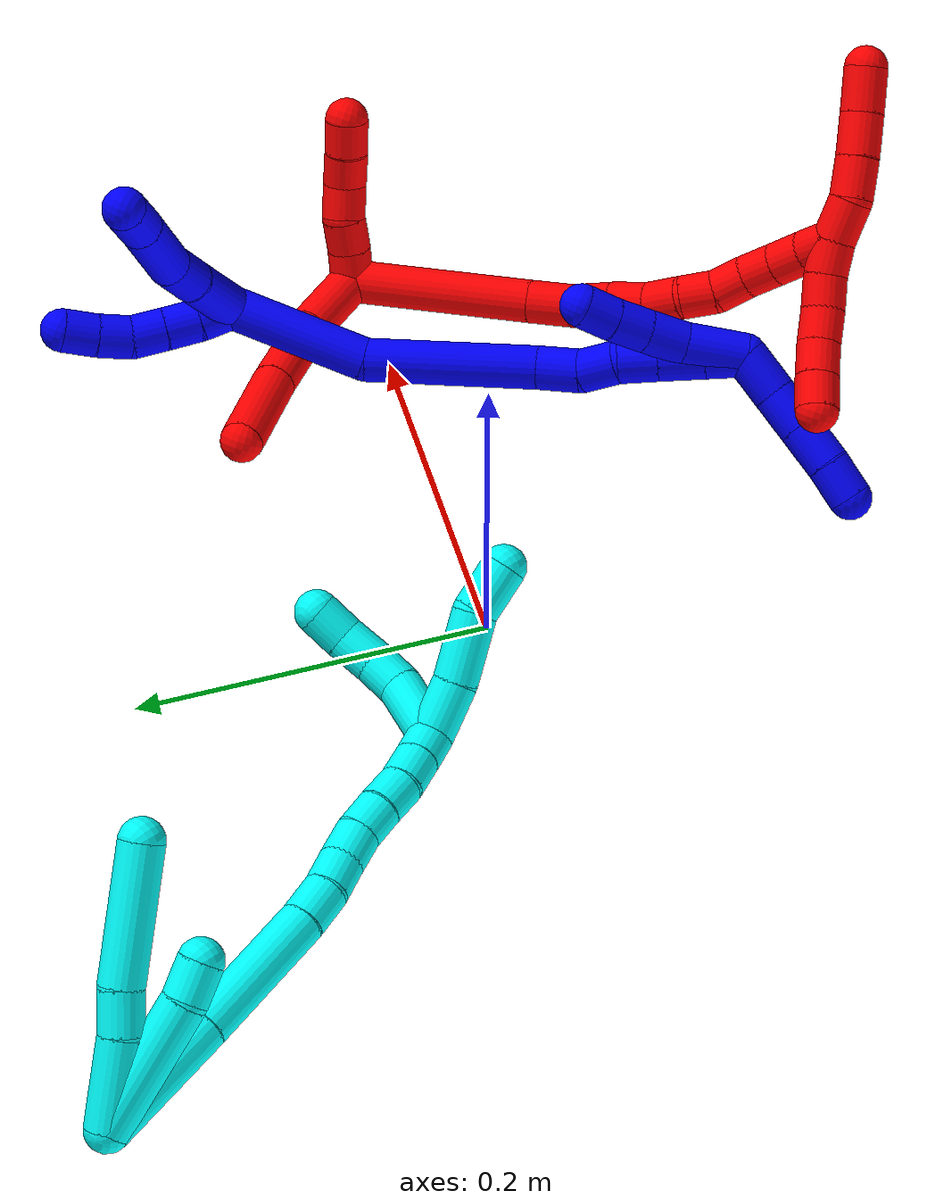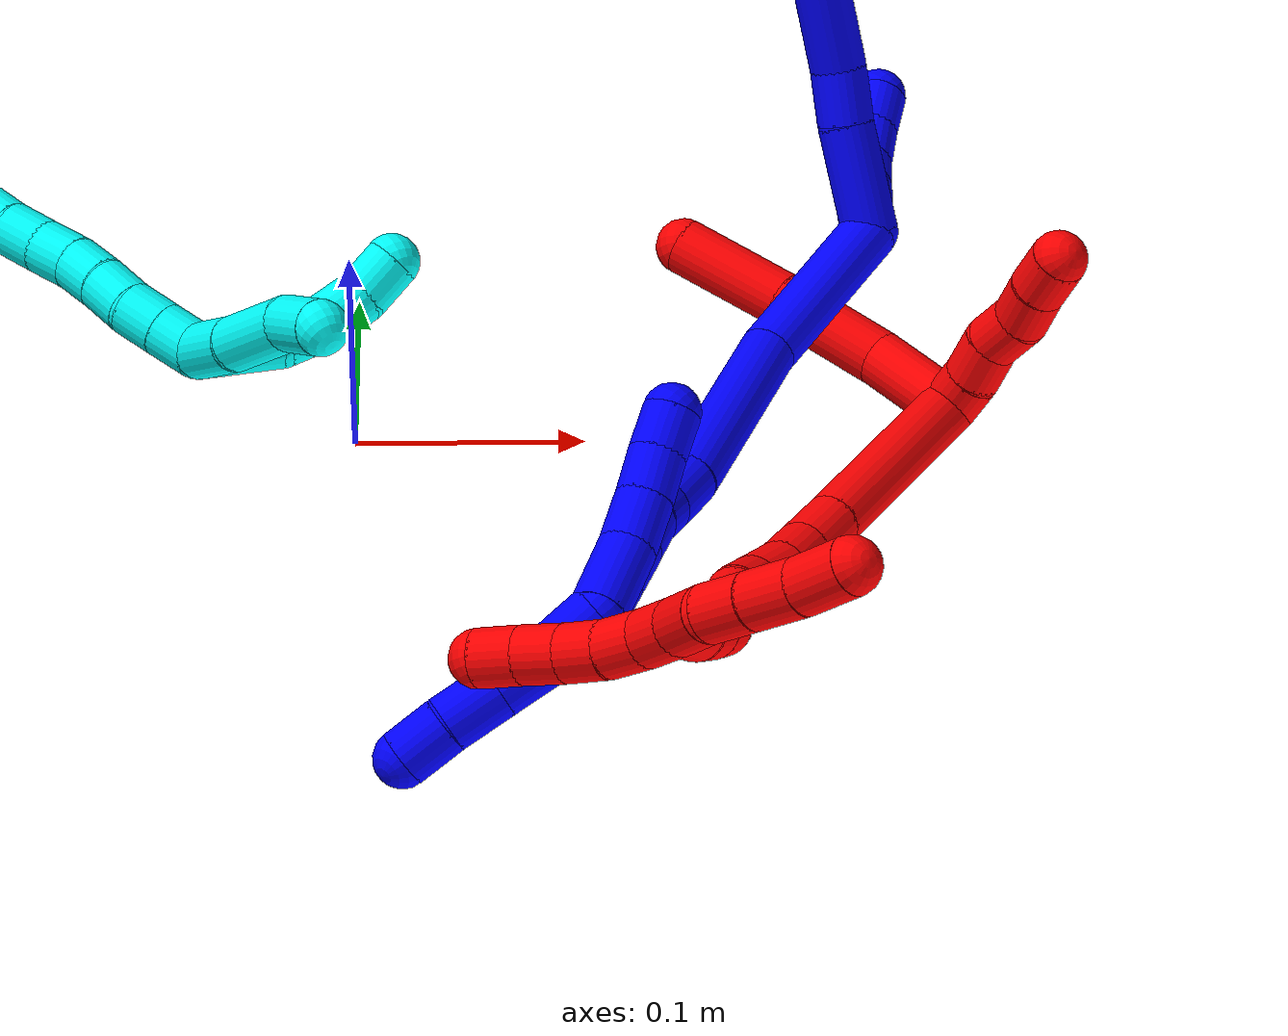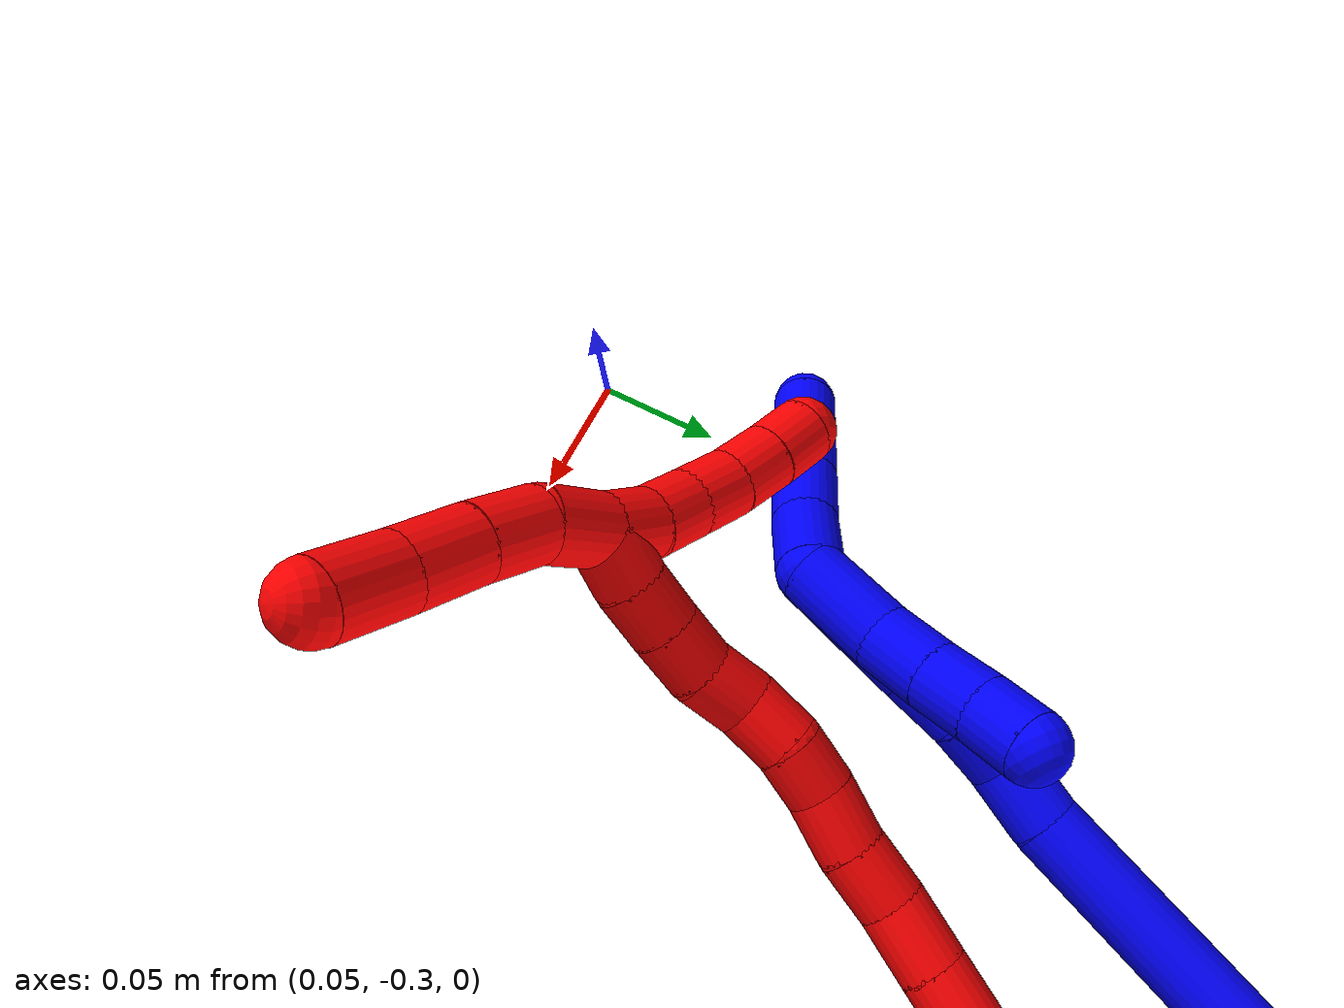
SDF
<sdf version="1.7">
 <world name="default">
  <plugin name="TubeGeneratorPlugin" filename="libtube_generator_plugin.so"/>
  <model name="photoneo_s_sensor">
   <static>1</static>
   <pose>0 0 2 1.57079 1.57079 3.14159</pose>
   <link name="link">
    <inertial><mass>0.1</mass></inertial>
    <sensor name="sensor" type="depth">
     <update_rate>30</update_rate>
     <camera>
      <horizontal_fov>1.22</horizontal_fov>
      <image><width>1920</width><height>1200</height><format>B8G8R8</format></image>
      <clip><near>0.1</near><far>4</far></clip>
      <depth_camera><output>points</output></depth_camera>
     </camera>
     <plugin name="camera_plugin" filename="libgazebo_ros_depth_camera.so">
      <baseline>0.2</baseline>
      <alwaysOn>1</alwaysOn>
      <updateRate>0.0</updateRate>
      <cameraName>camera_ir</cameraName>
      <imageTopicName>/camera/color/image_raw</imageTopicName>
      <cameraInfoTopicName>/camera/color/camera_info</cameraInfoTopicName>
      <depthImageTopicName>/camera/depth/image_raw</depthImageTopicName>
      <depthImageCameraInfoTopicName>/camera/depth/camera_info</depthImageCameraInfoTopicName>
      <pointCloudTopicName>/camera/depth/points</pointCloudTopicName>
      <frameName>fr_optical</frameName>
      <pointCloudCutoff>0.1</pointCloudCutoff>
      <pointCloudCutoffMax>2.0</pointCloudCutoffMax>
      <distortionK1>0</distortionK1>
      <distortionK2>0</distortionK2>
      <distortionK3>0</distortionK3>
      <distortionT1>0</distortionT1>
      <distortionT2>0</distortionT2>
      <CxPrime>0</CxPrime>
      <Cx>0</Cx>
      <Cy>0</Cy>
      <focalLength>0</focalLength>
      <hackBaseline>0</hackBaseline>
     </plugin>
    </sensor>
   </link>
  </model>
  <gravity>0 0 -9.8</gravity>
  <magnetic_field>6e-06 2.3e-05 -4.2e-05</magnetic_field>
  <atmosphere type="adiabatic"/>
  <physics name="default_physics" default="0" type="ode">
   <max_step_size>0.003</max_step_size>
   <real_time_factor>1</real_time_factor>
   <real_time_update_rate>1000</real_time_update_rate>
   <max_contacts>10000</max_contacts>
   <ode>
    <solver>
     <type>quick</type>
     <iters>100</iters>
     <sor>1.3</sor>
     <use_dynamic_moi_rescaling>0</use_dynamic_moi_rescaling>
    </solver>
    <constraints>
     <contact_max_correcting_vel>0</contact_max_correcting_vel>
     <contact_surface_layer>0.001</contact_surface_layer>
     <cfm>0</cfm>
     <erp>0.2</erp>
    </constraints>
   </ode>
  </physics>
  <scene><ambient>0.4 0.4 0.4 1</ambient><background>0.7 0.7 0.7 1</background><shadows>0</shadows></scene>
  <audio><device>default</device></audio>
  <spherical_coordinates>
   <surface_model>EARTH_WGS84</surface_model>
   <latitude_deg>0</latitude_deg>
   <longitude_deg>0</longitude_deg>
   <elevation>0</elevation>
   <heading_deg>0</heading_deg>
  </spherical_coordinates>
  <model name="bin">
   <static>1</static>
   <link name="bottom">
    <collision name="collision-bottom">
     <pose>0 0 -0.01 0 -0 0</pose>
     <geometry><box><size>0.8 0.6 0.02</size></box></geometry>
     <surface>
      <friction><ode><mu>100</mu><mu2>100</mu2></ode></friction>
      <contact><collide_bitmask>65535</collide_bitmask></contact>
     </surface>
    </collision>
   </link>
   <link name="west_wall">
    <collision name="collision-west_wall">
     <pose>-0.41 0 0.1 0 -0 0</pose>
     <geometry><box><size>0.02 0.6 0.2</size></box></geometry>
     <surface>
      <friction><ode><mu>100</mu><mu2>100</mu2></ode></friction>
      <contact><collide_bitmask>65535</collide_bitmask></contact>
     </surface>
    </collision>
   </link>
   <link name="east_wall">
    <collision name="collision-east_wall">
     <pose>0.41 0 0.1 0 -0 0</pose>
     <geometry><box><size>0.02 0.6 0.2</size></box></geometry>
     <surface>
      <friction><ode><mu>100</mu><mu2>100</mu2></ode></friction>
      <contact><collide_bitmask>65535</collide_bitmask></contact>
     </surface>
    </collision>
   </link>
   <link name="south_wall">
    <collision name="collision-south_wall">
     <pose>0 -0.31 0.1 0 -0 0</pose>
     <geometry><box><size>0.8 0.02 0.2</size></box></geometry>
     <surface>
      <friction><ode><mu>100</mu><mu2>100</mu2></ode></friction>
      <contact><collide_bitmask>65535</collide_bitmask></contact>
     </surface>
    </collision>
   </link>
   <link name="north_wall">
    <collision name="collision-north_wall">
     <pose>0 0.31 0.1 0 -0 0</pose>
     <geometry><box><size>0.8 0.02 0.2</size></box></geometry>
     <surface>
      <friction><ode><mu>100</mu><mu2>100</mu2></ode></friction>
      <contact><collide_bitmask>65535</collide_bitmask></contact>
     </surface>
    </collision>
   </link>
  </model>
  <model name="1">
   <static>0</static>
   <link name="1">
    <collision name="collision-cylinder-e_1_2_8">
     <pose>0.005056 0.022466 -0.007969 -1.91166 0.20901 -0.294834</pose>
     <geometry><cylinder><radius>0.0125</radius><length>0.048735</length></cylinder></geometry>
     <surface>
      <friction><ode><mu>1.16</mu><mu2>1.16</mu2><slip1>0</slip1><slip2>0</slip2></ode></friction>
      <contact><ode><kp>1e+06</kp><kd>1</kd><max_vel>0</max_vel><min_depth>0.001</min_depth></ode></contact>
     </surface>
    </collision>
    <visual name="visual-cylinder-e_1_2_8">
     <pose>0.005056 0.022466 -0.007969 -1.91166 0.20901 -0.294834</pose>
     <geometry><cylinder><radius>0.0125</radius><length>0.048735</length></cylinder></geometry>
     <material><ambient>0 0 1 1</ambient></material>
    </visual>
    <collision name="collision-cylinder-e_2_8_9">
     <pose>0.012987 0.055929 -0.02104 -2.0052 0.232806 -0.362298</pose>
     <geometry><cylinder><radius>0.0125</radius><length>0.024919</length></cylinder></geometry>
     <surface>
      <friction><ode><mu>1.16</mu><mu2>1.16</mu2><slip1>0</slip1><slip2>0</slip2></ode></friction>
      <contact><ode><kp>1e+06</kp><kd>1</kd><max_vel>0</max_vel><min_depth>0.001</min_depth></ode></contact>
     </surface>
    </collision>
    <visual name="visual-cylinder-e_2_8_9">
     <pose>0.012987 0.055929 -0.02104 -2.0052 0.232806 -0.362298</pose>
     <geometry><cylinder><radius>0.0125</radius><length>0.024919</length></cylinder></geometry>
     <material><ambient>0 0 1 1</ambient></material>
    </visual>
    <collision name="collision-cylinder-e_3_9_10">
     <pose>0.024714 0.089507 -0.031649 -1.80997 0.363909 -0.460192</pose>
     <geometry><cylinder><radius>0.0125</radius><length>0.049742</length></cylinder></geometry>
     <surface>
      <friction><ode><mu>1.16</mu><mu2>1.16</mu2><slip1>0</slip1><slip2>0</slip2></ode></friction>
      <contact><ode><kp>1e+06</kp><kd>1</kd><max_vel>0</max_vel><min_depth>0.001</min_depth></ode></contact>
     </surface>
    </collision>
    <visual name="visual-cylinder-e_3_9_10">
     <pose>0.024714 0.089507 -0.031649 -1.80997 0.363909 -0.460192</pose>
     <geometry><cylinder><radius>0.0125</radius><length>0.049742</length></cylinder></geometry>
     <material><ambient>0 0 1 1</ambient></material>
    </visual>
    <collision name="collision-cylinder-e_4_10_6">
     <pose>0.037794 0.124371 -0.040015 -1.79954 0.323438 -0.405338</pose>
     <geometry><cylinder><radius>0.0125</radius><length>0.026604</length></cylinder></geometry>
     <surface>
      <friction><ode><mu>1.16</mu><mu2>1.16</mu2><slip1>0</slip1><slip2>0</slip2></ode></friction>
      <contact><ode><kp>1e+06</kp><kd>1</kd><max_vel>0</max_vel><min_depth>0.001</min_depth></ode></contact>
     </surface>
    </collision>
    <visual name="visual-cylinder-e_4_10_6">
     <pose>0.037794 0.124371 -0.040015 -1.79954 0.323438 -0.405338</pose>
     <geometry><cylinder><radius>0.0125</radius><length>0.026604</length></cylinder></geometry>
     <material><ambient>0 0 1 1</ambient></material>
    </visual>
    <collision name="collision-cylinder-e_1_2_11">
     <pose>-0.006663 0.002929 -0.006857 -2.73787 -0.729226 2.15725</pose>
     <geometry><cylinder><radius>0.0125</radius><length>0.02</length></cylinder></geometry>
     <surface>
      <friction><ode><mu>1.16</mu><mu2>1.16</mu2><slip1>0</slip1><slip2>0</slip2></ode></friction>
      <contact><ode><kp>1e+06</kp><kd>1</kd><max_vel>0</max_vel><min_depth>0.001</min_depth></ode></contact>
     </surface>
    </collision>
    <visual name="visual-cylinder-e_1_2_11">
     <pose>-0.006663 0.002929 -0.006857 -2.73787 -0.729226 2.15725</pose>
     <geometry><cylinder><radius>0.0125</radius><length>0.02</length></cylinder></geometry>
     <material><ambient>0 0 1 1</ambient></material>
    </visual>
    <collision name="collision-cylinder-e_2_11_12">
     <pose>-0.019106 0.008926 -0.021276 -2.75626 -0.616345 2.04192</pose>
     <geometry><cylinder><radius>0.0125</radius><length>0.02</length></cylinder></geometry>
     <surface>
      <friction><ode><mu>1.16</mu><mu2>1.16</mu2><slip1>0</slip1><slip2>0</slip2></ode></friction>
      <contact><ode><kp>1e+06</kp><kd>1</kd><max_vel>0</max_vel><min_depth>0.001</min_depth></ode></contact>
     </surface>
    </collision>
    <visual name="visual-cylinder-e_2_11_12">
     <pose>-0.019106 0.008926 -0.021276 -2.75626 -0.616345 2.04192</pose>
     <geometry><cylinder><radius>0.0125</radius><length>0.02</length></cylinder></geometry>
     <material><ambient>0 0 1 1</ambient></material>
    </visual>
    <collision name="collision-cylinder-e_3_12_13">
     <pose>-0.030539 0.01499 -0.036524 -2.76977 -0.600661 2.05003</pose>
     <geometry><cylinder><radius>0.0125</radius><length>0.02</length></cylinder></geometry>
     <surface>
      <friction><ode><mu>1.16</mu><mu2>1.16</mu2><slip1>0</slip1><slip2>0</slip2></ode></friction>
      <contact><ode><kp>1e+06</kp><kd>1</kd><max_vel>0</max_vel><min_depth>0.001</min_depth></ode></contact>
     </surface>
    </collision>
    <visual name="visual-cylinder-e_3_12_13">
     <pose>-0.030539 0.01499 -0.036524 -2.76977 -0.600661 2.05003</pose>
     <geometry><cylinder><radius>0.0125</radius><length>0.02</length></cylinder></geometry>
     <material><ambient>0 0 1 1</ambient></material>
    </visual>
    <collision name="collision-cylinder-e_4_13_14">
     <pose>-0.039019 0.022213 -0.052821 -2.68542 -0.286779 1.11286</pose>
     <geometry><cylinder><radius>0.0125</radius><length>0.02</length></cylinder></geometry>
     <surface>
      <friction><ode><mu>1.16</mu><mu2>1.16</mu2><slip1>0</slip1><slip2>0</slip2></ode></friction>
      <contact><ode><kp>1e+06</kp><kd>1</kd><max_vel>0</max_vel><min_depth>0.001</min_depth></ode></contact>
     </surface>
    </collision>
    <visual name="visual-cylinder-e_4_13_14">
     <pose>-0.039019 0.022213 -0.052821 -2.68542 -0.286779 1.11286</pose>
     <geometry><cylinder><radius>0.0125</radius><length>0.02</length></cylinder></geometry>
     <material><ambient>0 0 1 1</ambient></material>
    </visual>
    <collision name="collision-cylinder-e_5_14_5">
     <pose>-0.04376 0.030689 -0.070279 -2.69372 -0.192407 0.801543</pose>
     <geometry><cylinder><radius>0.0125</radius><length>0.02</length></cylinder></geometry>
     <surface>
      <friction><ode><mu>1.16</mu><mu2>1.16</mu2><slip1>0</slip1><slip2>0</slip2></ode></friction>
      <contact><ode><kp>1e+06</kp><kd>1</kd><max_vel>0</max_vel><min_depth>0.001</min_depth></ode></contact>
     </surface>
    </collision>
    <visual name="visual-cylinder-e_5_14_5">
     <pose>-0.04376 0.030689 -0.070279 -2.69372 -0.192407 0.801543</pose>
     <geometry><cylinder><radius>0.0125</radius><length>0.02</length></cylinder></geometry>
     <material><ambient>0 0 1 1</ambient></material>
    </visual>
    <collision name="collision-cylinder-e_1_2_15">
     <pose>0.000389 -0.004578 0.040782 0.111792 0.009478 0.00053</pose>
     <geometry><cylinder><radius>0.0125</radius><length>0.08208</length></cylinder></geometry>
     <surface>
      <friction><ode><mu>1.16</mu><mu2>1.16</mu2><slip1>0</slip1><slip2>0</slip2></ode></friction>
      <contact><ode><kp>1e+06</kp><kd>1</kd><max_vel>0</max_vel><min_depth>0.001</min_depth></ode></contact>
     </surface>
    </collision>
    <visual name="visual-cylinder-e_1_2_15">
     <pose>0.000389 -0.004578 0.040782 0.111792 0.009478 0.00053</pose>
     <geometry><cylinder><radius>0.0125</radius><length>0.08208</length></cylinder></geometry>
     <material><ambient>0 0 1 1</ambient></material>
    </visual>
    <collision name="collision-cylinder-e_2_15_16">
     <pose>0.017124 -0.015077 0.127782 0.127409 0.337385 0.021728</pose>
     <geometry><cylinder><radius>0.0125</radius><length>0.098761</length></cylinder></geometry>
     <surface>
      <friction><ode><mu>1.16</mu><mu2>1.16</mu2><slip1>0</slip1><slip2>0</slip2></ode></friction>
      <contact><ode><kp>1e+06</kp><kd>1</kd><max_vel>0</max_vel><min_depth>0.001</min_depth></ode></contact>
     </surface>
    </collision>
    <visual name="visual-cylinder-e_2_15_16">
     <pose>0.017124 -0.015077 0.127782 0.127409 0.337385 0.021728</pose>
     <geometry><cylinder><radius>0.0125</radius><length>0.098761</length></cylinder></geometry>
     <material><ambient>0 0 1 1</ambient></material>
    </visual>
    <collision name="collision-cylinder-e_3_16_17">
     <pose>0.037317 -0.020734 0.185989 -0.02199 0.310444 -0.003441</pose>
     <geometry><cylinder><radius>0.0125</radius><length>0.025186</length></cylinder></geometry>
     <surface>
      <friction><ode><mu>1.16</mu><mu2>1.16</mu2><slip1>0</slip1><slip2>0</slip2></ode></friction>
      <contact><ode><kp>1e+06</kp><kd>1</kd><max_vel>0</max_vel><min_depth>0.001</min_depth></ode></contact>
     </surface>
    </collision>
    <visual name="visual-cylinder-e_3_16_17">
     <pose>0.037317 -0.020734 0.185989 -0.02199 0.310444 -0.003441</pose>
     <geometry><cylinder><radius>0.0125</radius><length>0.025186</length></cylinder></geometry>
     <material><ambient>0 0 1 1</ambient></material>
    </visual>
    <collision name="collision-cylinder-e_4_17_18">
     <pose>0.047622 -0.019147 0.206856 -0.148001 0.623635 -0.047784</pose>
     <geometry><cylinder><radius>0.0125</radius><length>0.022118</length></cylinder></geometry>
     <surface>
      <friction><ode><mu>1.16</mu><mu2>1.16</mu2><slip1>0</slip1><slip2>0</slip2></ode></friction>
      <contact><ode><kp>1e+06</kp><kd>1</kd><max_vel>0</max_vel><min_depth>0.001</min_depth></ode></contact>
     </surface>
    </collision>
    <visual name="visual-cylinder-e_4_17_18">
     <pose>0.047622 -0.019147 0.206856 -0.148001 0.623635 -0.047784</pose>
     <geometry><cylinder><radius>0.0125</radius><length>0.022118</length></cylinder></geometry>
     <material><ambient>0 0 1 1</ambient></material>
    </visual>
    <collision name="collision-cylinder-e_5_18_19">
     <pose>0.058959 -0.019253 0.225933 0.139346 0.4425 0.031392</pose>
     <geometry><cylinder><radius>0.0125</radius><length>0.02279</length></cylinder></geometry>
     <surface>
      <friction><ode><mu>1.16</mu><mu2>1.16</mu2><slip1>0</slip1><slip2>0</slip2></ode></friction>
      <contact><ode><kp>1e+06</kp><kd>1</kd><max_vel>0</max_vel><min_depth>0.001</min_depth></ode></contact>
     </surface>
    </collision>
    <visual name="visual-cylinder-e_5_18_19">
     <pose>0.058959 -0.019253 0.225933 0.139346 0.4425 0.031392</pose>
     <geometry><cylinder><radius>0.0125</radius><length>0.02279</length></cylinder></geometry>
     <material><ambient>0 0 1 1</ambient></material>
    </visual>
    <collision name="collision-cylinder-e_6_19_20">
     <pose>0.069459 -0.022143 0.2482 0.120305 0.433041 0.026494</pose>
     <geometry><cylinder><radius>0.0125</radius><length>0.026789</length></cylinder></geometry>
     <surface>
      <friction><ode><mu>1.16</mu><mu2>1.16</mu2><slip1>0</slip1><slip2>0</slip2></ode></friction>
      <contact><ode><kp>1e+06</kp><kd>1</kd><max_vel>0</max_vel><min_depth>0.001</min_depth></ode></contact>
     </surface>
    </collision>
    <visual name="visual-cylinder-e_6_19_20">
     <pose>0.069459 -0.022143 0.2482 0.120305 0.433041 0.026494</pose>
     <geometry><cylinder><radius>0.0125</radius><length>0.026789</length></cylinder></geometry>
     <material><ambient>0 0 1 1</ambient></material>
    </visual>
    <collision name="collision-cylinder-e_7_20_1">
     <pose>0.079774 -0.024801 0.2703 0.118961 0.43504 0.026322</pose>
     <geometry><cylinder><radius>0.0125</radius><length>0.022278</length></cylinder></geometry>
     <surface>
      <friction><ode><mu>1.16</mu><mu2>1.16</mu2><slip1>0</slip1><slip2>0</slip2></ode></friction>
      <contact><ode><kp>1e+06</kp><kd>1</kd><max_vel>0</max_vel><min_depth>0.001</min_depth></ode></contact>
     </surface>
    </collision>
    <visual name="visual-cylinder-e_7_20_1">
     <pose>0.079774 -0.024801 0.2703 0.118961 0.43504 0.026322</pose>
     <geometry><cylinder><radius>0.0125</radius><length>0.022278</length></cylinder></geometry>
     <material><ambient>0 0 1 1</ambient></material>
    </visual>
    <collision name="collision-cylinder-e_1_1_21">
     <pose>0.077466 -0.027193 0.291985 0.102023 -0.538725 -0.028188</pose>
     <geometry><cylinder><radius>0.0125</radius><length>0.027298</length></cylinder></geometry>
     <surface>
      <friction><ode><mu>1.16</mu><mu2>1.16</mu2><slip1>0</slip1><slip2>0</slip2></ode></friction>
      <contact><ode><kp>1e+06</kp><kd>1</kd><max_vel>0</max_vel><min_depth>0.001</min_depth></ode></contact>
     </surface>
    </collision>
    <visual name="visual-cylinder-e_1_1_21">
     <pose>0.077466 -0.027193 0.291985 0.102023 -0.538725 -0.028188</pose>
     <geometry><cylinder><radius>0.0125</radius><length>0.027298</length></cylinder></geometry>
     <material><ambient>0 0 1 1</ambient></material>
    </visual>
    <collision name="collision-cylinder-e_2_21_22">
     <pose>0.064341 -0.027833 0.314278 -0.051893 -0.521692 0.013855</pose>
     <geometry><cylinder><radius>0.0125</radius><length>0.024572</length></cylinder></geometry>
     <surface>
      <friction><ode><mu>1.16</mu><mu2>1.16</mu2><slip1>0</slip1><slip2>0</slip2></ode></friction>
      <contact><ode><kp>1e+06</kp><kd>1</kd><max_vel>0</max_vel><min_depth>0.001</min_depth></ode></contact>
     </surface>
    </collision>
    <visual name="visual-cylinder-e_2_21_22">
     <pose>0.064341 -0.027833 0.314278 -0.051893 -0.521692 0.013855</pose>
     <geometry><cylinder><radius>0.0125</radius><length>0.024572</length></cylinder></geometry>
     <material><ambient>0 0 1 1</ambient></material>
    </visual>
    <collision name="collision-cylinder-e_3_22_23">
     <pose>0.051822 -0.026743 0.335974 -0.048565 -0.523866 0.013022</pose>
     <geometry><cylinder><radius>0.0125</radius><length>0.025573</length></cylinder></geometry>
     <surface>
      <friction><ode><mu>1.16</mu><mu2>1.16</mu2><slip1>0</slip1><slip2>0</slip2></ode></friction>
      <contact><ode><kp>1e+06</kp><kd>1</kd><max_vel>0</max_vel><min_depth>0.001</min_depth></ode></contact>
     </surface>
    </collision>
    <visual name="visual-cylinder-e_3_22_23">
     <pose>0.051822 -0.026743 0.335974 -0.048565 -0.523866 0.013022</pose>
     <geometry><cylinder><radius>0.0125</radius><length>0.025573</length></cylinder></geometry>
     <material><ambient>0 0 1 1</ambient></material>
    </visual>
    <collision name="collision-cylinder-e_4_23_4">
     <pose>0.039039 -0.026627 0.356319 0.045271 -0.601971 -0.014055</pose>
     <geometry><cylinder><radius>0.0125</radius><length>0.022556</length></cylinder></geometry>
     <surface>
      <friction><ode><mu>1.16</mu><mu2>1.16</mu2><slip1>0</slip1><slip2>0</slip2></ode></friction>
      <contact><ode><kp>1e+06</kp><kd>1</kd><max_vel>0</max_vel><min_depth>0.001</min_depth></ode></contact>
     </surface>
    </collision>
    <visual name="visual-cylinder-e_4_23_4">
     <pose>0.039039 -0.026627 0.356319 0.045271 -0.601971 -0.014055</pose>
     <geometry><cylinder><radius>0.0125</radius><length>0.022556</length></cylinder></geometry>
     <material><ambient>0 0 1 1</ambient></material>
    </visual>
    <collision name="collision-cylinder-e_1_1_24">
     <pose>0.081227 -0.021001 0.263655 -2.85035 -0.184105 1.12358</pose>
     <geometry><cylinder><radius>0.0125</radius><length>0.035416</length></cylinder></geometry>
     <surface>
      <friction><ode><mu>1.16</mu><mu2>1.16</mu2><slip1>0</slip1><slip2>0</slip2></ode></friction>
      <contact><ode><kp>1e+06</kp><kd>1</kd><max_vel>0</max_vel><min_depth>0.001</min_depth></ode></contact>
     </surface>
    </collision>
    <visual name="visual-cylinder-e_1_1_24">
     <pose>0.081227 -0.021001 0.263655 -2.85035 -0.184105 1.12358</pose>
     <geometry><cylinder><radius>0.0125</radius><length>0.035416</length></cylinder></geometry>
     <material><ambient>0 0 1 1</ambient></material>
    </visual>
    <collision name="collision-cylinder-e_2_24_25">
     <pose>0.077674 -0.010797 0.236393 -2.68461 -0.02637 0.113282</pose>
     <geometry><cylinder><radius>0.0125</radius><length>0.023602</length></cylinder></geometry>
     <surface>
      <friction><ode><mu>1.16</mu><mu2>1.16</mu2><slip1>0</slip1><slip2>0</slip2></ode></friction>
      <contact><ode><kp>1e+06</kp><kd>1</kd><max_vel>0</max_vel><min_depth>0.001</min_depth></ode></contact>
     </surface>
    </collision>
    <visual name="visual-cylinder-e_2_24_25">
     <pose>0.077674 -0.010797 0.236393 -2.68461 -0.02637 0.113282</pose>
     <geometry><cylinder><radius>0.0125</radius><length>0.023602</length></cylinder></geometry>
     <material><ambient>0 0 1 1</ambient></material>
    </visual>
    <collision name="collision-cylinder-e_3_25_26">
     <pose>0.077226 -0.000476 0.21672 -2.62887 -0.013185 0.050289</pose>
     <geometry><cylinder><radius>0.0125</radius><length>0.020856</length></cylinder></geometry>
     <surface>
      <friction><ode><mu>1.16</mu><mu2>1.16</mu2><slip1>0</slip1><slip2>0</slip2></ode></friction>
      <contact><ode><kp>1e+06</kp><kd>1</kd><max_vel>0</max_vel><min_depth>0.001</min_depth></ode></contact>
     </surface>
    </collision>
    <visual name="visual-cylinder-e_3_25_26">
     <pose>0.077226 -0.000476 0.21672 -2.62887 -0.013185 0.050289</pose>
     <geometry><cylinder><radius>0.0125</radius><length>0.020856</length></cylinder></geometry>
     <material><ambient>0 0 1 1</ambient></material>
    </visual>
    <collision name="collision-cylinder-e_4_26_3">
     <pose>0.077706 0.009435 0.198809 -2.64372 0.061473 -0.24073</pose>
     <geometry><cylinder><radius>0.0125</radius><length>0.020126</length></cylinder></geometry>
     <surface>
      <friction><ode><mu>1.16</mu><mu2>1.16</mu2><slip1>0</slip1><slip2>0</slip2></ode></friction>
      <contact><ode><kp>1e+06</kp><kd>1</kd><max_vel>0</max_vel><min_depth>0.001</min_depth></ode></contact>
     </surface>
    </collision>
    <visual name="visual-cylinder-e_4_26_3">
     <pose>0.077706 0.009435 0.198809 -2.64372 0.061473 -0.24073</pose>
     <geometry><cylinder><radius>0.0125</radius><length>0.020126</length></cylinder></geometry>
     <material><ambient>0 0 1 1</ambient></material>
    </visual>
    <collision name="collision-sphere-3">
     <pose>0.078325 0.014232 0.189984 0 -0 0</pose>
     <geometry><sphere><radius>0.0125</radius></sphere></geometry>
     <surface>
      <friction><ode><mu>1.16</mu><mu2>1.16</mu2><slip1>0</slip1><slip2>0</slip2></ode></friction>
      <contact><ode><kp>1e+06</kp><kd>1</kd><max_vel>0</max_vel><min_depth>0.001</min_depth></ode></contact>
     </surface>
    </collision>
    <visual name="visual-sphere-3">
     <pose>0.078325 0.014232 0.189984 0 -0 0</pose>
     <geometry><sphere><radius>0.0125</radius></sphere></geometry>
     <material><ambient>0 0 1 1</ambient></material>
    </visual>
    <collision name="collision-sphere-26">
     <pose>0.077088 0.004639 0.207634 0 -0 0</pose>
     <geometry><sphere><radius>0.0125</radius></sphere></geometry>
     <surface>
      <friction><ode><mu>1.16</mu><mu2>1.16</mu2><slip1>0</slip1><slip2>0</slip2></ode></friction>
      <contact><ode><kp>1e+06</kp><kd>1</kd><max_vel>0</max_vel><min_depth>0.001</min_depth></ode></contact>
     </surface>
    </collision>
    <visual name="visual-sphere-26">
     <pose>0.077088 0.004639 0.207634 0 -0 0</pose>
     <geometry><sphere><radius>0.0125</radius></sphere></geometry>
     <material><ambient>0 0 1 1</ambient></material>
    </visual>
    <collision name="collision-sphere-25">
     <pose>0.077363 -0.005591 0.225806 0 -0 0</pose>
     <geometry><sphere><radius>0.0125</radius></sphere></geometry>
     <surface>
      <friction><ode><mu>1.16</mu><mu2>1.16</mu2><slip1>0</slip1><slip2>0</slip2></ode></friction>
      <contact><ode><kp>1e+06</kp><kd>1</kd><max_vel>0</max_vel><min_depth>0.001</min_depth></ode></contact>
     </surface>
    </collision>
    <visual name="visual-sphere-25">
     <pose>0.077363 -0.005591 0.225806 0 -0 0</pose>
     <geometry><sphere><radius>0.0125</radius></sphere></geometry>
     <material><ambient>0 0 1 1</ambient></material>
    </visual>
    <collision name="collision-sphere-24">
     <pose>0.077985 -0.016002 0.246979 0 -0 0</pose>
     <geometry><sphere><radius>0.0125</radius></sphere></geometry>
     <surface>
      <friction><ode><mu>1.16</mu><mu2>1.16</mu2><slip1>0</slip1><slip2>0</slip2></ode></friction>
      <contact><ode><kp>1e+06</kp><kd>1</kd><max_vel>0</max_vel><min_depth>0.001</min_depth></ode></contact>
     </surface>
    </collision>
    <visual name="visual-sphere-24">
     <pose>0.077985 -0.016002 0.246979 0 -0 0</pose>
     <geometry><sphere><radius>0.0125</radius></sphere></geometry>
     <material><ambient>0 0 1 1</ambient></material>
    </visual>
    <collision name="collision-sphere-4">
     <pose>0.032653 -0.027047 0.365605 0 -0 0</pose>
     <geometry><sphere><radius>0.0125</radius></sphere></geometry>
     <surface>
      <friction><ode><mu>1.16</mu><mu2>1.16</mu2><slip1>0</slip1><slip2>0</slip2></ode></friction>
      <contact><ode><kp>1e+06</kp><kd>1</kd><max_vel>0</max_vel><min_depth>0.001</min_depth></ode></contact>
     </surface>
    </collision>
    <visual name="visual-sphere-4">
     <pose>0.032653 -0.027047 0.365605 0 -0 0</pose>
     <geometry><sphere><radius>0.0125</radius></sphere></geometry>
     <material><ambient>0 0 1 1</ambient></material>
    </visual>
    <collision name="collision-sphere-23">
     <pose>0.045425 -0.026206 0.347033 0 -0 0</pose>
     <geometry><sphere><radius>0.0125</radius></sphere></geometry>
     <surface>
      <friction><ode><mu>1.16</mu><mu2>1.16</mu2><slip1>0</slip1><slip2>0</slip2></ode></friction>
      <contact><ode><kp>1e+06</kp><kd>1</kd><max_vel>0</max_vel><min_depth>0.001</min_depth></ode></contact>
     </surface>
    </collision>
    <visual name="visual-sphere-23">
     <pose>0.045425 -0.026206 0.347033 0 -0 0</pose>
     <geometry><sphere><radius>0.0125</radius></sphere></geometry>
     <material><ambient>0 0 1 1</ambient></material>
    </visual>
    <collision name="collision-sphere-22">
     <pose>0.058218 -0.027281 0.324916 0 -0 0</pose>
     <geometry><sphere><radius>0.0125</radius></sphere></geometry>
     <surface>
      <friction><ode><mu>1.16</mu><mu2>1.16</mu2><slip1>0</slip1><slip2>0</slip2></ode></friction>
      <contact><ode><kp>1e+06</kp><kd>1</kd><max_vel>0</max_vel><min_depth>0.001</min_depth></ode></contact>
     </surface>
    </collision>
    <visual name="visual-sphere-22">
     <pose>0.058218 -0.027281 0.324916 0 -0 0</pose>
     <geometry><sphere><radius>0.0125</radius></sphere></geometry>
     <material><ambient>0 0 1 1</ambient></material>
    </visual>
    <collision name="collision-sphere-21">
     <pose>0.070464 -0.028386 0.303641 0 -0 0</pose>
     <geometry><sphere><radius>0.0125</radius></sphere></geometry>
     <surface>
      <friction><ode><mu>1.16</mu><mu2>1.16</mu2><slip1>0</slip1><slip2>0</slip2></ode></friction>
      <contact><ode><kp>1e+06</kp><kd>1</kd><max_vel>0</max_vel><min_depth>0.001</min_depth></ode></contact>
     </surface>
    </collision>
    <visual name="visual-sphere-21">
     <pose>0.070464 -0.028386 0.303641 0 -0 0</pose>
     <geometry><sphere><radius>0.0125</radius></sphere></geometry>
     <material><ambient>0 0 1 1</ambient></material>
    </visual>
    <collision name="collision-sphere-1">
     <pose>0.084469 -0.025999 0.28033 0 -0 0</pose>
     <geometry><sphere><radius>0.0125</radius></sphere></geometry>
     <surface>
      <friction><ode><mu>1.16</mu><mu2>1.16</mu2><slip1>0</slip1><slip2>0</slip2></ode></friction>
      <contact><ode><kp>1e+06</kp><kd>1</kd><max_vel>0</max_vel><min_depth>0.001</min_depth></ode></contact>
     </surface>
    </collision>
    <visual name="visual-sphere-1">
     <pose>0.084469 -0.025999 0.28033 0 -0 0</pose>
     <geometry><sphere><radius>0.0125</radius></sphere></geometry>
     <material><ambient>0 0 1 1</ambient></material>
    </visual>
    <collision name="collision-sphere-11">
     <pose>-0.013326 0.005859 -0.013715 0 -0 0</pose>
     <geometry><sphere><radius>0.0125</radius></sphere></geometry>
     <surface>
      <friction><ode><mu>1.16</mu><mu2>1.16</mu2><slip1>0</slip1><slip2>0</slip2></ode></friction>
      <contact><ode><kp>1e+06</kp><kd>1</kd><max_vel>0</max_vel><min_depth>0.001</min_depth></ode></contact>
     </surface>
    </collision>
    <visual name="visual-sphere-11">
     <pose>-0.013326 0.005859 -0.013715 0 -0 0</pose>
     <geometry><sphere><radius>0.0125</radius></sphere></geometry>
     <material><ambient>0 0 1 1</ambient></material>
    </visual>
    <collision name="collision-sphere-6">
     <pose>0.042021 0.136655 -0.042874 0 -0 0</pose>
     <geometry><sphere><radius>0.0125</radius></sphere></geometry>
     <surface>
      <friction><ode><mu>1.16</mu><mu2>1.16</mu2><slip1>0</slip1><slip2>0</slip2></ode></friction>
      <contact><ode><kp>1e+06</kp><kd>1</kd><max_vel>0</max_vel><min_depth>0.001</min_depth></ode></contact>
     </surface>
    </collision>
    <visual name="visual-sphere-6">
     <pose>0.042021 0.136655 -0.042874 0 -0 0</pose>
     <geometry><sphere><radius>0.0125</radius></sphere></geometry>
     <material><ambient>0 0 1 1</ambient></material>
    </visual>
    <collision name="collision-sphere-10">
     <pose>0.033566 0.112088 -0.037155 0 -0 0</pose>
     <geometry><sphere><radius>0.0125</radius></sphere></geometry>
     <surface>
      <friction><ode><mu>1.16</mu><mu2>1.16</mu2><slip1>0</slip1><slip2>0</slip2></ode></friction>
      <contact><ode><kp>1e+06</kp><kd>1</kd><max_vel>0</max_vel><min_depth>0.001</min_depth></ode></contact>
     </surface>
    </collision>
    <visual name="visual-sphere-10">
     <pose>0.033566 0.112088 -0.037155 0 -0 0</pose>
     <geometry><sphere><radius>0.0125</radius></sphere></geometry>
     <material><ambient>0 0 1 1</ambient></material>
    </visual>
    <collision name="collision-sphere-9">
     <pose>0.015861 0.066927 -0.026143 0 -0 0</pose>
     <geometry><sphere><radius>0.0125</radius></sphere></geometry>
     <surface>
      <friction><ode><mu>1.16</mu><mu2>1.16</mu2><slip1>0</slip1><slip2>0</slip2></ode></friction>
      <contact><ode><kp>1e+06</kp><kd>1</kd><max_vel>0</max_vel><min_depth>0.001</min_depth></ode></contact>
     </surface>
    </collision>
    <visual name="visual-sphere-9">
     <pose>0.015861 0.066927 -0.026143 0 -0 0</pose>
     <geometry><sphere><radius>0.0125</radius></sphere></geometry>
     <material><ambient>0 0 1 1</ambient></material>
    </visual>
    <collision name="collision-sphere-2">
     <geometry><sphere><radius>0.0125</radius></sphere></geometry>
     <surface>
      <friction><ode><mu>1.16</mu><mu2>1.16</mu2><slip1>0</slip1><slip2>0</slip2></ode></friction>
      <contact><ode><kp>1e+06</kp><kd>1</kd><max_vel>0</max_vel><min_depth>0.001</min_depth></ode></contact>
     </surface>
    </collision>
    <visual name="visual-sphere-2">
     <geometry><sphere><radius>0.0125</radius></sphere></geometry>
     <material><ambient>0 0 1 1</ambient></material>
    </visual>
    <collision name="collision-sphere-19">
     <pose>0.063839 -0.020683 0.23613 0 -0 0</pose>
     <geometry><sphere><radius>0.0125</radius></sphere></geometry>
     <surface>
      <friction><ode><mu>1.16</mu><mu2>1.16</mu2><slip1>0</slip1><slip2>0</slip2></ode></friction>
      <contact><ode><kp>1e+06</kp><kd>1</kd><max_vel>0</max_vel><min_depth>0.001</min_depth></ode></contact>
     </surface>
    </collision>
    <visual name="visual-sphere-19">
     <pose>0.063839 -0.020683 0.23613 0 -0 0</pose>
     <geometry><sphere><radius>0.0125</radius></sphere></geometry>
     <material><ambient>0 0 1 1</ambient></material>
    </visual>
    <collision name="collision-sphere-8">
     <pose>0.010112 0.044932 -0.015938 0 -0 0</pose>
     <geometry><sphere><radius>0.0125</radius></sphere></geometry>
     <surface>
      <friction><ode><mu>1.16</mu><mu2>1.16</mu2><slip1>0</slip1><slip2>0</slip2></ode></friction>
      <contact><ode><kp>1e+06</kp><kd>1</kd><max_vel>0</max_vel><min_depth>0.001</min_depth></ode></contact>
     </surface>
    </collision>
    <visual name="visual-sphere-8">
     <pose>0.010112 0.044932 -0.015938 0 -0 0</pose>
     <geometry><sphere><radius>0.0125</radius></sphere></geometry>
     <material><ambient>0 0 1 1</ambient></material>
    </visual>
    <collision name="collision-sphere-12">
     <pose>-0.024887 0.011993 -0.028838 0 -0 0</pose>
     <geometry><sphere><radius>0.0125</radius></sphere></geometry>
     <surface>
      <friction><ode><mu>1.16</mu><mu2>1.16</mu2><slip1>0</slip1><slip2>0</slip2></ode></friction>
      <contact><ode><kp>1e+06</kp><kd>1</kd><max_vel>0</max_vel><min_depth>0.001</min_depth></ode></contact>
     </surface>
    </collision>
    <visual name="visual-sphere-12">
     <pose>-0.024887 0.011993 -0.028838 0 -0 0</pose>
     <geometry><sphere><radius>0.0125</radius></sphere></geometry>
     <material><ambient>0 0 1 1</ambient></material>
    </visual>
    <collision name="collision-sphere-13">
     <pose>-0.036191 0.017987 -0.04421 0 -0 0</pose>
     <geometry><sphere><radius>0.0125</radius></sphere></geometry>
     <surface>
      <friction><ode><mu>1.16</mu><mu2>1.16</mu2><slip1>0</slip1><slip2>0</slip2></ode></friction>
      <contact><ode><kp>1e+06</kp><kd>1</kd><max_vel>0</max_vel><min_depth>0.001</min_depth></ode></contact>
     </surface>
    </collision>
    <visual name="visual-sphere-13">
     <pose>-0.036191 0.017987 -0.04421 0 -0 0</pose>
     <geometry><sphere><radius>0.0125</radius></sphere></geometry>
     <material><ambient>0 0 1 1</ambient></material>
    </visual>
    <collision name="collision-sphere-14">
     <pose>-0.041848 0.026438 -0.061431 0 -0 0</pose>
     <geometry><sphere><radius>0.0125</radius></sphere></geometry>
     <surface>
      <friction><ode><mu>1.16</mu><mu2>1.16</mu2><slip1>0</slip1><slip2>0</slip2></ode></friction>
      <contact><ode><kp>1e+06</kp><kd>1</kd><max_vel>0</max_vel><min_depth>0.001</min_depth></ode></contact>
     </surface>
    </collision>
    <visual name="visual-sphere-14">
     <pose>-0.041848 0.026438 -0.061431 0 -0 0</pose>
     <geometry><sphere><radius>0.0125</radius></sphere></geometry>
     <material><ambient>0 0 1 1</ambient></material>
    </visual>
    <collision name="collision-sphere-5">
     <pose>-0.045672 0.034939 -0.079126 0 -0 0</pose>
     <geometry><sphere><radius>0.0125</radius></sphere></geometry>
     <surface>
      <friction><ode><mu>1.16</mu><mu2>1.16</mu2><slip1>0</slip1><slip2>0</slip2></ode></friction>
      <contact><ode><kp>1e+06</kp><kd>1</kd><max_vel>0</max_vel><min_depth>0.001</min_depth></ode></contact>
     </surface>
    </collision>
    <visual name="visual-sphere-5">
     <pose>-0.045672 0.034939 -0.079126 0 -0 0</pose>
     <geometry><sphere><radius>0.0125</radius></sphere></geometry>
     <material><ambient>0 0 1 1</ambient></material>
    </visual>
    <collision name="collision-sphere-15">
     <pose>0.000778 -0.009156 0.081564 0 -0 0</pose>
     <geometry><sphere><radius>0.0125</radius></sphere></geometry>
     <surface>
      <friction><ode><mu>1.16</mu><mu2>1.16</mu2><slip1>0</slip1><slip2>0</slip2></ode></friction>
      <contact><ode><kp>1e+06</kp><kd>1</kd><max_vel>0</max_vel><min_depth>0.001</min_depth></ode></contact>
     </surface>
    </collision>
    <visual name="visual-sphere-15">
     <pose>0.000778 -0.009156 0.081564 0 -0 0</pose>
     <geometry><sphere><radius>0.0125</radius></sphere></geometry>
     <material><ambient>0 0 1 1</ambient></material>
    </visual>
    <collision name="collision-sphere-16">
     <pose>0.03347 -0.020998 0.174001 0 -0 0</pose>
     <geometry><sphere><radius>0.0125</radius></sphere></geometry>
     <surface>
      <friction><ode><mu>1.16</mu><mu2>1.16</mu2><slip1>0</slip1><slip2>0</slip2></ode></friction>
      <contact><ode><kp>1e+06</kp><kd>1</kd><max_vel>0</max_vel><min_depth>0.001</min_depth></ode></contact>
     </surface>
    </collision>
    <visual name="visual-sphere-16">
     <pose>0.03347 -0.020998 0.174001 0 -0 0</pose>
     <geometry><sphere><radius>0.0125</radius></sphere></geometry>
     <material><ambient>0 0 1 1</ambient></material>
    </visual>
    <collision name="collision-sphere-17">
     <pose>0.041164 -0.020471 0.197977 0 -0 0</pose>
     <geometry><sphere><radius>0.0125</radius></sphere></geometry>
     <surface>
      <friction><ode><mu>1.16</mu><mu2>1.16</mu2><slip1>0</slip1><slip2>0</slip2></ode></friction>
      <contact><ode><kp>1e+06</kp><kd>1</kd><max_vel>0</max_vel><min_depth>0.001</min_depth></ode></contact>
     </surface>
    </collision>
    <visual name="visual-sphere-17">
     <pose>0.041164 -0.020471 0.197977 0 -0 0</pose>
     <geometry><sphere><radius>0.0125</radius></sphere></geometry>
     <material><ambient>0 0 1 1</ambient></material>
    </visual>
    <collision name="collision-sphere-18">
     <pose>0.05408 -0.017823 0.215735 0 -0 0</pose>
     <geometry><sphere><radius>0.0125</radius></sphere></geometry>
     <surface>
      <friction><ode><mu>1.16</mu><mu2>1.16</mu2><slip1>0</slip1><slip2>0</slip2></ode></friction>
      <contact><ode><kp>1e+06</kp><kd>1</kd><max_vel>0</max_vel><min_depth>0.001</min_depth></ode></contact>
     </surface>
    </collision>
    <visual name="visual-sphere-18">
     <pose>0.05408 -0.017823 0.215735 0 -0 0</pose>
     <geometry><sphere><radius>0.0125</radius></sphere></geometry>
     <material><ambient>0 0 1 1</ambient></material>
    </visual>
    <collision name="collision-sphere-20">
     <pose>0.07508 -0.023602 0.26027 0 -0 0</pose>
     <geometry><sphere><radius>0.0125</radius></sphere></geometry>
     <surface>
      <friction><ode><mu>1.16</mu><mu2>1.16</mu2><slip1>0</slip1><slip2>0</slip2></ode></friction>
      <contact><ode><kp>1e+06</kp><kd>1</kd><max_vel>0</max_vel><min_depth>0.001</min_depth></ode></contact>
     </surface>
    </collision>
    <visual name="visual-sphere-20">
     <pose>0.07508 -0.023602 0.26027 0 -0 0</pose>
     <geometry><sphere><radius>0.0125</radius></sphere></geometry>
     <material><ambient>0 0 1 1</ambient></material>
    </visual>
    <inertial>
     <pose>0.030009 0.005227 0.122 0 -0 0</pose>
     <mass>0.75</mass>
     <inertia>
      <ixx>0.000182</ixx>
      <ixy>0</ixy>
      <ixz>0</ixz>
      <iyy>0.000158</iyy>
      <iyz>0</iyz>
      <izz>-3.6e-05</izz>
     </inertia>
    </inertial>
   </link>
   <pose>0.226494 0.085172 0.048544 1.7201 -0.75068 -0.80557</pose>
  </model>
  <model name="2">
   <static>0</static>
   <link name="2">
    <collision name="collision-cylinder-e_1_2_8">
     <pose>-0.014547 0.005423 -0.015568 -2.80637 -0.72302 2.3001</pose>
     <geometry><cylinder><radius>0.0125</radius><length>0.043972</length></cylinder></geometry>
     <surface>
      <friction><ode><mu>1.16</mu><mu2>1.16</mu2><slip1>0</slip1><slip2>0</slip2></ode></friction>
      <contact><ode><kp>1e+06</kp><kd>1</kd><max_vel>0</max_vel><min_depth>0.001</min_depth></ode></contact>
     </surface>
    </collision>
    <visual name="visual-cylinder-e_1_2_8">
     <pose>-0.014547 0.005423 -0.015568 -2.80637 -0.72302 2.3001</pose>
     <geometry><cylinder><radius>0.0125</radius><length>0.043972</length></cylinder></geometry>
     <material><ambient>1 0 0 1</ambient></material>
    </visual>
    <collision name="collision-cylinder-e_2_8_9">
     <pose>-0.050276 0.012065 -0.047183 -3.06583 -0.921062 2.9891</pose>
     <geometry><cylinder><radius>0.0125</radius><length>0.053205</length></cylinder></geometry>
     <surface>
      <friction><ode><mu>1.16</mu><mu2>1.16</mu2><slip1>0</slip1><slip2>0</slip2></ode></friction>
      <contact><ode><kp>1e+06</kp><kd>1</kd><max_vel>0</max_vel><min_depth>0.001</min_depth></ode></contact>
     </surface>
    </collision>
    <visual name="visual-cylinder-e_2_8_9">
     <pose>-0.050276 0.012065 -0.047183 -3.06583 -0.921062 2.9891</pose>
     <geometry><cylinder><radius>0.0125</radius><length>0.053205</length></cylinder></geometry>
     <material><ambient>1 0 0 1</ambient></material>
    </visual>
    <collision name="collision-cylinder-e_3_9_6">
     <pose>-0.092477 0.013211 -0.079224 3.13706 -0.920352 -3.13245</pose>
     <geometry><cylinder><radius>0.0125</radius><length>0.052823</length></cylinder></geometry>
     <surface>
      <friction><ode><mu>1.16</mu><mu2>1.16</mu2><slip1>0</slip1><slip2>0</slip2></ode></friction>
      <contact><ode><kp>1e+06</kp><kd>1</kd><max_vel>0</max_vel><min_depth>0.001</min_depth></ode></contact>
     </surface>
    </collision>
    <visual name="visual-cylinder-e_3_9_6">
     <pose>-0.092477 0.013211 -0.079224 3.13706 -0.920352 -3.13245</pose>
     <geometry><cylinder><radius>0.0125</radius><length>0.052823</length></cylinder></geometry>
     <material><ambient>1 0 0 1</ambient></material>
    </visual>
    <collision name="collision-cylinder-e_1_2_10">
     <pose>-0.003016 0.003396 0.008909 -0.364231 -0.306392 0.056854</pose>
     <geometry><cylinder><radius>0.0125</radius><length>0.02</length></cylinder></geometry>
     <surface>
      <friction><ode><mu>1.16</mu><mu2>1.16</mu2><slip1>0</slip1><slip2>0</slip2></ode></friction>
      <contact><ode><kp>1e+06</kp><kd>1</kd><max_vel>0</max_vel><min_depth>0.001</min_depth></ode></contact>
     </surface>
    </collision>
    <visual name="visual-cylinder-e_1_2_10">
     <pose>-0.003016 0.003396 0.008909 -0.364231 -0.306392 0.056854</pose>
     <geometry><cylinder><radius>0.0125</radius><length>0.02</length></cylinder></geometry>
     <material><ambient>1 0 0 1</ambient></material>
    </visual>
    <collision name="collision-cylinder-e_2_10_11">
     <pose>-0.0102 0.010452 0.026139 -0.414233 -0.429856 0.091678</pose>
     <geometry><cylinder><radius>0.0125</radius><length>0.02</length></cylinder></geometry>
     <surface>
      <friction><ode><mu>1.16</mu><mu2>1.16</mu2><slip1>0</slip1><slip2>0</slip2></ode></friction>
      <contact><ode><kp>1e+06</kp><kd>1</kd><max_vel>0</max_vel><min_depth>0.001</min_depth></ode></contact>
     </surface>
    </collision>
    <visual name="visual-cylinder-e_2_10_11">
     <pose>-0.0102 0.010452 0.026139 -0.414233 -0.429856 0.091678</pose>
     <geometry><cylinder><radius>0.0125</radius><length>0.02</length></cylinder></geometry>
     <material><ambient>1 0 0 1</ambient></material>
    </visual>
    <collision name="collision-cylinder-e_3_11_12">
     <pose>-0.015705 0.016692 0.044028 -0.263578 -0.134167 0.017811</pose>
     <geometry><cylinder><radius>0.0125</radius><length>0.02</length></cylinder></geometry>
     <surface>
      <friction><ode><mu>1.16</mu><mu2>1.16</mu2><slip1>0</slip1><slip2>0</slip2></ode></friction>
      <contact><ode><kp>1e+06</kp><kd>1</kd><max_vel>0</max_vel><min_depth>0.001</min_depth></ode></contact>
     </surface>
    </collision>
    <visual name="visual-cylinder-e_3_11_12">
     <pose>-0.015705 0.016692 0.044028 -0.263578 -0.134167 0.017811</pose>
     <geometry><cylinder><radius>0.0125</radius><length>0.02</length></cylinder></geometry>
     <material><ambient>1 0 0 1</ambient></material>
    </visual>
    <collision name="collision-cylinder-e_4_12_13">
     <pose>-0.021189 0.020982 0.062534 -0.188789 -0.427609 0.041107</pose>
     <geometry><cylinder><radius>0.0125</radius><length>0.02</length></cylinder></geometry>
     <surface>
      <friction><ode><mu>1.16</mu><mu2>1.16</mu2><slip1>0</slip1><slip2>0</slip2></ode></friction>
      <contact><ode><kp>1e+06</kp><kd>1</kd><max_vel>0</max_vel><min_depth>0.001</min_depth></ode></contact>
     </surface>
    </collision>
    <visual name="visual-cylinder-e_4_12_13">
     <pose>-0.021189 0.020982 0.062534 -0.188789 -0.427609 0.041107</pose>
     <geometry><cylinder><radius>0.0125</radius><length>0.02</length></cylinder></geometry>
     <material><ambient>1 0 0 1</ambient></material>
    </visual>
    <collision name="collision-cylinder-e_5_13_5">
     <pose>-0.028779 0.024977 0.080578 -0.246112 -0.351461 0.043915</pose>
     <geometry><cylinder><radius>0.0125</radius><length>0.02</length></cylinder></geometry>
     <surface>
      <friction><ode><mu>1.16</mu><mu2>1.16</mu2><slip1>0</slip1><slip2>0</slip2></ode></friction>
      <contact><ode><kp>1e+06</kp><kd>1</kd><max_vel>0</max_vel><min_depth>0.001</min_depth></ode></contact>
     </surface>
    </collision>
    <visual name="visual-cylinder-e_5_13_5">
     <pose>-0.028779 0.024977 0.080578 -0.246112 -0.351461 0.043915</pose>
     <geometry><cylinder><radius>0.0125</radius><length>0.02</length></cylinder></geometry>
     <material><ambient>1 0 0 1</ambient></material>
    </visual>
    <collision name="collision-cylinder-e_1_2_14">
     <pose>-0.005306 -0.052286 0.011813 1.3486 -0.098656 -0.078877</pose>
     <geometry><cylinder><radius>0.0125</radius><length>0.107731</length></cylinder></geometry>
     <surface>
      <friction><ode><mu>1.16</mu><mu2>1.16</mu2><slip1>0</slip1><slip2>0</slip2></ode></friction>
      <contact><ode><kp>1e+06</kp><kd>1</kd><max_vel>0</max_vel><min_depth>0.001</min_depth></ode></contact>
     </surface>
    </collision>
    <visual name="visual-cylinder-e_1_2_14">
     <pose>-0.005306 -0.052286 0.011813 1.3486 -0.098656 -0.078877</pose>
     <geometry><cylinder><radius>0.0125</radius><length>0.107731</length></cylinder></geometry>
     <material><ambient>1 0 0 1</ambient></material>
    </visual>
    <collision name="collision-cylinder-e_2_14_15">
     <pose>-0.012053 -0.116964 0.02655 1.33909 -0.1128 -0.089318</pose>
     <geometry><cylinder><radius>0.0125</radius><length>0.025628</length></cylinder></geometry>
     <surface>
      <friction><ode><mu>1.16</mu><mu2>1.16</mu2><slip1>0</slip1><slip2>0</slip2></ode></friction>
      <contact><ode><kp>1e+06</kp><kd>1</kd><max_vel>0</max_vel><min_depth>0.001</min_depth></ode></contact>
     </surface>
    </collision>
    <visual name="visual-cylinder-e_2_14_15">
     <pose>-0.012053 -0.116964 0.02655 1.33909 -0.1128 -0.089318</pose>
     <geometry><cylinder><radius>0.0125</radius><length>0.025628</length></cylinder></geometry>
     <material><ambient>1 0 0 1</ambient></material>
    </visual>
    <collision name="collision-cylinder-e_3_15_16">
     <pose>-0.015262 -0.139974 0.033925 1.17384 -0.152224 -0.101354</pose>
     <geometry><cylinder><radius>0.0125</radius><length>0.023296</length></cylinder></geometry>
     <surface>
      <friction><ode><mu>1.16</mu><mu2>1.16</mu2><slip1>0</slip1><slip2>0</slip2></ode></friction>
      <contact><ode><kp>1e+06</kp><kd>1</kd><max_vel>0</max_vel><min_depth>0.001</min_depth></ode></contact>
     </surface>
    </collision>
    <visual name="visual-cylinder-e_3_15_16">
     <pose>-0.015262 -0.139974 0.033925 1.17384 -0.152224 -0.101354</pose>
     <geometry><cylinder><radius>0.0125</radius><length>0.023296</length></cylinder></geometry>
     <material><ambient>1 0 0 1</ambient></material>
    </visual>
    <collision name="collision-cylinder-e_4_16_17">
     <pose>-0.020222 -0.161043 0.042016 1.23558 -0.280958 -0.200294</pose>
     <geometry><cylinder><radius>0.0125</radius><length>0.023037</length></cylinder></geometry>
     <surface>
      <friction><ode><mu>1.16</mu><mu2>1.16</mu2><slip1>0</slip1><slip2>0</slip2></ode></friction>
      <contact><ode><kp>1e+06</kp><kd>1</kd><max_vel>0</max_vel><min_depth>0.001</min_depth></ode></contact>
     </surface>
    </collision>
    <visual name="visual-cylinder-e_4_16_17">
     <pose>-0.020222 -0.161043 0.042016 1.23558 -0.280958 -0.200294</pose>
     <geometry><cylinder><radius>0.0125</radius><length>0.023037</length></cylinder></geometry>
     <material><ambient>1 0 0 1</ambient></material>
    </visual>
    <collision name="collision-cylinder-e_5_17_18">
     <pose>-0.026145 -0.179874 0.050472 1.04931 -0.275188 -0.159939</pose>
     <geometry><cylinder><radius>0.0125</radius><length>0.020087</length></cylinder></geometry>
     <surface>
      <friction><ode><mu>1.16</mu><mu2>1.16</mu2><slip1>0</slip1><slip2>0</slip2></ode></friction>
      <contact><ode><kp>1e+06</kp><kd>1</kd><max_vel>0</max_vel><min_depth>0.001</min_depth></ode></contact>
     </surface>
    </collision>
    <visual name="visual-cylinder-e_5_17_18">
     <pose>-0.026145 -0.179874 0.050472 1.04931 -0.275188 -0.159939</pose>
     <geometry><cylinder><radius>0.0125</radius><length>0.020087</length></cylinder></geometry>
     <material><ambient>1 0 0 1</ambient></material>
    </visual>
    <collision name="collision-cylinder-e_6_18_19">
     <pose>-0.029014 -0.19713 0.060081 1.07555 -0.013888 -0.008283</pose>
     <geometry><cylinder><radius>0.0125</radius><length>0.020175</length></cylinder></geometry>
     <surface>
      <friction><ode><mu>1.16</mu><mu2>1.16</mu2><slip1>0</slip1><slip2>0</slip2></ode></friction>
      <contact><ode><kp>1e+06</kp><kd>1</kd><max_vel>0</max_vel><min_depth>0.001</min_depth></ode></contact>
     </surface>
    </collision>
    <visual name="visual-cylinder-e_6_18_19">
     <pose>-0.029014 -0.19713 0.060081 1.07555 -0.013888 -0.008283</pose>
     <geometry><cylinder><radius>0.0125</radius><length>0.020175</length></cylinder></geometry>
     <material><ambient>1 0 0 1</ambient></material>
    </visual>
    <collision name="collision-cylinder-e_7_19_20">
     <pose>-0.02986 -0.213064 0.071933 0.785496 -0.070578 -0.029249</pose>
     <geometry><cylinder><radius>0.0125</radius><length>0.020016</length></cylinder></geometry>
     <surface>
      <friction><ode><mu>1.16</mu><mu2>1.16</mu2><slip1>0</slip1><slip2>0</slip2></ode></friction>
      <contact><ode><kp>1e+06</kp><kd>1</kd><max_vel>0</max_vel><min_depth>0.001</min_depth></ode></contact>
     </surface>
    </collision>
    <visual name="visual-cylinder-e_7_19_20">
     <pose>-0.02986 -0.213064 0.071933 0.785496 -0.070578 -0.029249</pose>
     <geometry><cylinder><radius>0.0125</radius><length>0.020016</length></cylinder></geometry>
     <material><ambient>1 0 0 1</ambient></material>
    </visual>
    <collision name="collision-cylinder-e_8_20_21">
     <pose>-0.03369 -0.227275 0.085254 0.851531 -0.317513 -0.144961</pose>
     <geometry><cylinder><radius>0.0125</radius><length>0.020013</length></cylinder></geometry>
     <surface>
      <friction><ode><mu>1.16</mu><mu2>1.16</mu2><slip1>0</slip1><slip2>0</slip2></ode></friction>
      <contact><ode><kp>1e+06</kp><kd>1</kd><max_vel>0</max_vel><min_depth>0.001</min_depth></ode></contact>
     </surface>
    </collision>
    <visual name="visual-cylinder-e_8_20_21">
     <pose>-0.03369 -0.227275 0.085254 0.851531 -0.317513 -0.144961</pose>
     <geometry><cylinder><radius>0.0125</radius><length>0.020013</length></cylinder></geometry>
     <material><ambient>1 0 0 1</ambient></material>
    </visual>
    <collision name="collision-cylinder-e_9_21_22">
     <pose>-0.040307 -0.241437 0.097742 0.844667 -0.356652 -0.161638</pose>
     <geometry><cylinder><radius>0.0125</radius><length>0.02001</length></cylinder></geometry>
     <surface>
      <friction><ode><mu>1.16</mu><mu2>1.16</mu2><slip1>0</slip1><slip2>0</slip2></ode></friction>
      <contact><ode><kp>1e+06</kp><kd>1</kd><max_vel>0</max_vel><min_depth>0.001</min_depth></ode></contact>
     </surface>
    </collision>
    <visual name="visual-cylinder-e_9_21_22">
     <pose>-0.040307 -0.241437 0.097742 0.844667 -0.356652 -0.161638</pose>
     <geometry><cylinder><radius>0.0125</radius><length>0.02001</length></cylinder></geometry>
     <material><ambient>1 0 0 1</ambient></material>
    </visual>
    <collision name="collision-cylinder-e_10_22_1">
     <pose>-0.048775 -0.255071 0.109577 0.868047 -0.520461 -0.245589</pose>
     <geometry><cylinder><radius>0.0125</radius><length>0.020008</length></cylinder></geometry>
     <surface>
      <friction><ode><mu>1.16</mu><mu2>1.16</mu2><slip1>0</slip1><slip2>0</slip2></ode></friction>
      <contact><ode><kp>1e+06</kp><kd>1</kd><max_vel>0</max_vel><min_depth>0.001</min_depth></ode></contact>
     </surface>
    </collision>
    <visual name="visual-cylinder-e_10_22_1">
     <pose>-0.048775 -0.255071 0.109577 0.868047 -0.520461 -0.245589</pose>
     <geometry><cylinder><radius>0.0125</radius><length>0.020008</length></cylinder></geometry>
     <material><ambient>1 0 0 1</ambient></material>
    </visual>
    <collision name="collision-cylinder-e_1_1_23">
     <pose>-0.054285 -0.262701 0.105252 3.04051 -0.05354 -0.973713</pose>
     <geometry><cylinder><radius>0.0125</radius><length>0.02</length></cylinder></geometry>
     <surface>
      <friction><ode><mu>1.16</mu><mu2>1.16</mu2><slip1>0</slip1><slip2>0</slip2></ode></friction>
      <contact><ode><kp>1e+06</kp><kd>1</kd><max_vel>0</max_vel><min_depth>0.001</min_depth></ode></contact>
     </surface>
    </collision>
    <visual name="visual-cylinder-e_1_1_23">
     <pose>-0.054285 -0.262701 0.105252 3.04051 -0.05354 -0.973713</pose>
     <geometry><cylinder><radius>0.0125</radius><length>0.02</length></cylinder></geometry>
     <material><ambient>1 0 0 1</ambient></material>
    </visual>
    <collision name="collision-cylinder-e_2_23_24">
     <pose>-0.056809 -0.266389 0.085891 2.86459 -0.200222 -1.24882</pose>
     <geometry><cylinder><radius>0.0125</radius><length>0.02</length></cylinder></geometry>
     <surface>
      <friction><ode><mu>1.16</mu><mu2>1.16</mu2><slip1>0</slip1><slip2>0</slip2></ode></friction>
      <contact><ode><kp>1e+06</kp><kd>1</kd><max_vel>0</max_vel><min_depth>0.001</min_depth></ode></contact>
     </surface>
    </collision>
    <visual name="visual-cylinder-e_2_23_24">
     <pose>-0.056809 -0.266389 0.085891 2.86459 -0.200222 -1.24882</pose>
     <geometry><cylinder><radius>0.0125</radius><length>0.02</length></cylinder></geometry>
     <material><ambient>1 0 0 1</ambient></material>
    </visual>
    <collision name="collision-cylinder-e_3_24_25">
     <pose>-0.062145 -0.271246 0.067295 2.9085 -0.341272 -1.948</pose>
     <geometry><cylinder><radius>0.0125</radius><length>0.02</length></cylinder></geometry>
     <surface>
      <friction><ode><mu>1.16</mu><mu2>1.16</mu2><slip1>0</slip1><slip2>0</slip2></ode></friction>
      <contact><ode><kp>1e+06</kp><kd>1</kd><max_vel>0</max_vel><min_depth>0.001</min_depth></ode></contact>
     </surface>
    </collision>
    <visual name="visual-cylinder-e_3_24_25">
     <pose>-0.062145 -0.271246 0.067295 2.9085 -0.341272 -1.948</pose>
     <geometry><cylinder><radius>0.0125</radius><length>0.02</length></cylinder></geometry>
     <material><ambient>1 0 0 1</ambient></material>
    </visual>
    <collision name="collision-cylinder-e_4_25_26">
     <pose>-0.069742 -0.276251 0.049528 2.82378 -0.438982 -1.8957</pose>
     <geometry><cylinder><radius>0.0125</radius><length>0.02</length></cylinder></geometry>
     <surface>
      <friction><ode><mu>1.16</mu><mu2>1.16</mu2><slip1>0</slip1><slip2>0</slip2></ode></friction>
      <contact><ode><kp>1e+06</kp><kd>1</kd><max_vel>0</max_vel><min_depth>0.001</min_depth></ode></contact>
     </surface>
    </collision>
    <visual name="visual-cylinder-e_4_25_26">
     <pose>-0.069742 -0.276251 0.049528 2.82378 -0.438982 -1.8957</pose>
     <geometry><cylinder><radius>0.0125</radius><length>0.02</length></cylinder></geometry>
     <material><ambient>1 0 0 1</ambient></material>
    </visual>
    <collision name="collision-cylinder-e_5_26_4">
     <pose>-0.078211 -0.282324 0.032464 2.77561 -0.435541 -1.74859</pose>
     <geometry><cylinder><radius>0.0125</radius><length>0.02</length></cylinder></geometry>
     <surface>
      <friction><ode><mu>1.16</mu><mu2>1.16</mu2><slip1>0</slip1><slip2>0</slip2></ode></friction>
      <contact><ode><kp>1e+06</kp><kd>1</kd><max_vel>0</max_vel><min_depth>0.001</min_depth></ode></contact>
     </surface>
    </collision>
    <visual name="visual-cylinder-e_5_26_4">
     <pose>-0.078211 -0.282324 0.032464 2.77561 -0.435541 -1.74859</pose>
     <geometry><cylinder><radius>0.0125</radius><length>0.02</length></cylinder></geometry>
     <material><ambient>1 0 0 1</ambient></material>
    </visual>
    <collision name="collision-cylinder-e_1_1_27">
     <pose>-0.054331 -0.262612 0.127545 0.074201 -0.046841 -0.001739</pose>
     <geometry><cylinder><radius>0.0125</radius><length>0.024812</length></cylinder></geometry>
     <surface>
      <friction><ode><mu>1.16</mu><mu2>1.16</mu2><slip1>0</slip1><slip2>0</slip2></ode></friction>
      <contact><ode><kp>1e+06</kp><kd>1</kd><max_vel>0</max_vel><min_depth>0.001</min_depth></ode></contact>
     </surface>
    </collision>
    <visual name="visual-cylinder-e_1_1_27">
     <pose>-0.054331 -0.262612 0.127545 0.074201 -0.046841 -0.001739</pose>
     <geometry><cylinder><radius>0.0125</radius><length>0.024812</length></cylinder></geometry>
     <material><ambient>1 0 0 1</ambient></material>
    </visual>
    <collision name="collision-cylinder-e_2_27_28">
     <pose>-0.053107 -0.261328 0.151477 -0.188099 0.151997 -0.014365</pose>
     <geometry><cylinder><radius>0.0125</radius><length>0.023838</length></cylinder></geometry>
     <surface>
      <friction><ode><mu>1.16</mu><mu2>1.16</mu2><slip1>0</slip1><slip2>0</slip2></ode></friction>
      <contact><ode><kp>1e+06</kp><kd>1</kd><max_vel>0</max_vel><min_depth>0.001</min_depth></ode></contact>
     </surface>
    </collision>
    <visual name="visual-cylinder-e_2_27_28">
     <pose>-0.053107 -0.261328 0.151477 -0.188099 0.151997 -0.014365</pose>
     <geometry><cylinder><radius>0.0125</radius><length>0.023838</length></cylinder></geometry>
     <material><ambient>1 0 0 1</ambient></material>
    </visual>
    <collision name="collision-cylinder-e_3_28_29">
     <pose>-0.049102 -0.256151 0.175098 -0.242024 0.175431 -0.021388</pose>
     <geometry><cylinder><radius>0.0125</radius><length>0.025205</length></cylinder></geometry>
     <surface>
      <friction><ode><mu>1.16</mu><mu2>1.16</mu2><slip1>0</slip1><slip2>0</slip2></ode></friction>
      <contact><ode><kp>1e+06</kp><kd>1</kd><max_vel>0</max_vel><min_depth>0.001</min_depth></ode></contact>
     </surface>
    </collision>
    <visual name="visual-cylinder-e_3_28_29">
     <pose>-0.049102 -0.256151 0.175098 -0.242024 0.175431 -0.021388</pose>
     <geometry><cylinder><radius>0.0125</radius><length>0.025205</length></cylinder></geometry>
     <material><ambient>1 0 0 1</ambient></material>
    </visual>
    <collision name="collision-cylinder-e_4_29_3">
     <pose>-0.045765 -0.249949 0.199762 -0.250449 0.08714 -0.010976</pose>
     <geometry><cylinder><radius>0.0125</radius><length>0.026145</length></cylinder></geometry>
     <surface>
      <friction><ode><mu>1.16</mu><mu2>1.16</mu2><slip1>0</slip1><slip2>0</slip2></ode></friction>
      <contact><ode><kp>1e+06</kp><kd>1</kd><max_vel>0</max_vel><min_depth>0.001</min_depth></ode></contact>
     </surface>
    </collision>
    <visual name="visual-cylinder-e_4_29_3">
     <pose>-0.045765 -0.249949 0.199762 -0.250449 0.08714 -0.010976</pose>
     <geometry><cylinder><radius>0.0125</radius><length>0.026145</length></cylinder></geometry>
     <material><ambient>1 0 0 1</ambient></material>
    </visual>
    <collision name="collision-sphere-3">
     <pose>-0.044628 -0.246722 0.212379 0 -0 0</pose>
     <geometry><sphere><radius>0.0125</radius></sphere></geometry>
     <surface>
      <friction><ode><mu>1.16</mu><mu2>1.16</mu2><slip1>0</slip1><slip2>0</slip2></ode></friction>
      <contact><ode><kp>1e+06</kp><kd>1</kd><max_vel>0</max_vel><min_depth>0.001</min_depth></ode></contact>
     </surface>
    </collision>
    <visual name="visual-sphere-3">
     <pose>-0.044628 -0.246722 0.212379 0 -0 0</pose>
     <geometry><sphere><radius>0.0125</radius></sphere></geometry>
     <material><ambient>1 0 0 1</ambient></material>
    </visual>
    <collision name="collision-sphere-29">
     <pose>-0.046903 -0.253177 0.187146 0 -0 0</pose>
     <geometry><sphere><radius>0.0125</radius></sphere></geometry>
     <surface>
      <friction><ode><mu>1.16</mu><mu2>1.16</mu2><slip1>0</slip1><slip2>0</slip2></ode></friction>
      <contact><ode><kp>1e+06</kp><kd>1</kd><max_vel>0</max_vel><min_depth>0.001</min_depth></ode></contact>
     </surface>
    </collision>
    <visual name="visual-sphere-29">
     <pose>-0.046903 -0.253177 0.187146 0 -0 0</pose>
     <geometry><sphere><radius>0.0125</radius></sphere></geometry>
     <material><ambient>1 0 0 1</ambient></material>
    </visual>
    <collision name="collision-sphere-28">
     <pose>-0.051302 -0.259125 0.163051 0 -0 0</pose>
     <geometry><sphere><radius>0.0125</radius></sphere></geometry>
     <surface>
      <friction><ode><mu>1.16</mu><mu2>1.16</mu2><slip1>0</slip1><slip2>0</slip2></ode></friction>
      <contact><ode><kp>1e+06</kp><kd>1</kd><max_vel>0</max_vel><min_depth>0.001</min_depth></ode></contact>
     </surface>
    </collision>
    <visual name="visual-sphere-28">
     <pose>-0.051302 -0.259125 0.163051 0 -0 0</pose>
     <geometry><sphere><radius>0.0125</radius></sphere></geometry>
     <material><ambient>1 0 0 1</ambient></material>
    </visual>
    <collision name="collision-sphere-27">
     <pose>-0.054911 -0.263531 0.139903 0 -0 0</pose>
     <geometry><sphere><radius>0.0125</radius></sphere></geometry>
     <surface>
      <friction><ode><mu>1.16</mu><mu2>1.16</mu2><slip1>0</slip1><slip2>0</slip2></ode></friction>
      <contact><ode><kp>1e+06</kp><kd>1</kd><max_vel>0</max_vel><min_depth>0.001</min_depth></ode></contact>
     </surface>
    </collision>
    <visual name="visual-sphere-27">
     <pose>-0.054911 -0.263531 0.139903 0 -0 0</pose>
     <geometry><sphere><radius>0.0125</radius></sphere></geometry>
     <material><ambient>1 0 0 1</ambient></material>
    </visual>
    <collision name="collision-sphere-4">
     <pose>-0.08243 -0.285569 0.023998 0 -0 0</pose>
     <geometry><sphere><radius>0.0125</radius></sphere></geometry>
     <surface>
      <friction><ode><mu>1.16</mu><mu2>1.16</mu2><slip1>0</slip1><slip2>0</slip2></ode></friction>
      <contact><ode><kp>1e+06</kp><kd>1</kd><max_vel>0</max_vel><min_depth>0.001</min_depth></ode></contact>
     </surface>
    </collision>
    <visual name="visual-sphere-4">
     <pose>-0.08243 -0.285569 0.023998 0 -0 0</pose>
     <geometry><sphere><radius>0.0125</radius></sphere></geometry>
     <material><ambient>1 0 0 1</ambient></material>
    </visual>
    <collision name="collision-sphere-26">
     <pose>-0.073992 -0.27908 0.04093 0 -0 0</pose>
     <geometry><sphere><radius>0.0125</radius></sphere></geometry>
     <surface>
      <friction><ode><mu>1.16</mu><mu2>1.16</mu2><slip1>0</slip1><slip2>0</slip2></ode></friction>
      <contact><ode><kp>1e+06</kp><kd>1</kd><max_vel>0</max_vel><min_depth>0.001</min_depth></ode></contact>
     </surface>
    </collision>
    <visual name="visual-sphere-26">
     <pose>-0.073992 -0.27908 0.04093 0 -0 0</pose>
     <geometry><sphere><radius>0.0125</radius></sphere></geometry>
     <material><ambient>1 0 0 1</ambient></material>
    </visual>
    <collision name="collision-sphere-25">
     <pose>-0.065491 -0.273422 0.058127 0 -0 0</pose>
     <geometry><sphere><radius>0.0125</radius></sphere></geometry>
     <surface>
      <friction><ode><mu>1.16</mu><mu2>1.16</mu2><slip1>0</slip1><slip2>0</slip2></ode></friction>
      <contact><ode><kp>1e+06</kp><kd>1</kd><max_vel>0</max_vel><min_depth>0.001</min_depth></ode></contact>
     </surface>
    </collision>
    <visual name="visual-sphere-25">
     <pose>-0.065491 -0.273422 0.058127 0 -0 0</pose>
     <geometry><sphere><radius>0.0125</radius></sphere></geometry>
     <material><ambient>1 0 0 1</ambient></material>
    </visual>
    <collision name="collision-sphere-24">
     <pose>-0.058798 -0.269069 0.076464 0 -0 0</pose>
     <geometry><sphere><radius>0.0125</radius></sphere></geometry>
     <surface>
      <friction><ode><mu>1.16</mu><mu2>1.16</mu2><slip1>0</slip1><slip2>0</slip2></ode></friction>
      <contact><ode><kp>1e+06</kp><kd>1</kd><max_vel>0</max_vel><min_depth>0.001</min_depth></ode></contact>
     </surface>
    </collision>
    <visual name="visual-sphere-24">
     <pose>-0.058798 -0.269069 0.076464 0 -0 0</pose>
     <geometry><sphere><radius>0.0125</radius></sphere></geometry>
     <material><ambient>1 0 0 1</ambient></material>
    </visual>
    <collision name="collision-sphere-23">
     <pose>-0.05482 -0.263709 0.095317 0 -0 0</pose>
     <geometry><sphere><radius>0.0125</radius></sphere></geometry>
     <surface>
      <friction><ode><mu>1.16</mu><mu2>1.16</mu2><slip1>0</slip1><slip2>0</slip2></ode></friction>
      <contact><ode><kp>1e+06</kp><kd>1</kd><max_vel>0</max_vel><min_depth>0.001</min_depth></ode></contact>
     </surface>
    </collision>
    <visual name="visual-sphere-23">
     <pose>-0.05482 -0.263709 0.095317 0 -0 0</pose>
     <geometry><sphere><radius>0.0125</radius></sphere></geometry>
     <material><ambient>1 0 0 1</ambient></material>
    </visual>
    <collision name="collision-sphere-1">
     <pose>-0.05375 -0.261694 0.115187 0 -0 0</pose>
     <geometry><sphere><radius>0.0125</radius></sphere></geometry>
     <surface>
      <friction><ode><mu>1.16</mu><mu2>1.16</mu2><slip1>0</slip1><slip2>0</slip2></ode></friction>
      <contact><ode><kp>1e+06</kp><kd>1</kd><max_vel>0</max_vel><min_depth>0.001</min_depth></ode></contact>
     </surface>
    </collision>
    <visual name="visual-sphere-1">
     <pose>-0.05375 -0.261694 0.115187 0 -0 0</pose>
     <geometry><sphere><radius>0.0125</radius></sphere></geometry>
     <material><ambient>1 0 0 1</ambient></material>
    </visual>
    <collision name="collision-sphere-22">
     <pose>-0.0438 -0.248448 0.103968 0 -0 0</pose>
     <geometry><sphere><radius>0.0125</radius></sphere></geometry>
     <surface>
      <friction><ode><mu>1.16</mu><mu2>1.16</mu2><slip1>0</slip1><slip2>0</slip2></ode></friction>
      <contact><ode><kp>1e+06</kp><kd>1</kd><max_vel>0</max_vel><min_depth>0.001</min_depth></ode></contact>
     </surface>
    </collision>
    <visual name="visual-sphere-22">
     <pose>-0.0438 -0.248448 0.103968 0 -0 0</pose>
     <geometry><sphere><radius>0.0125</radius></sphere></geometry>
     <material><ambient>1 0 0 1</ambient></material>
    </visual>
    <collision name="collision-sphere-21">
     <pose>-0.036814 -0.234427 0.091517 0 -0 0</pose>
     <geometry><sphere><radius>0.0125</radius></sphere></geometry>
     <surface>
      <friction><ode><mu>1.16</mu><mu2>1.16</mu2><slip1>0</slip1><slip2>0</slip2></ode></friction>
      <contact><ode><kp>1e+06</kp><kd>1</kd><max_vel>0</max_vel><min_depth>0.001</min_depth></ode></contact>
     </surface>
    </collision>
    <visual name="visual-sphere-21">
     <pose>-0.036814 -0.234427 0.091517 0 -0 0</pose>
     <geometry><sphere><radius>0.0125</radius></sphere></geometry>
     <material><ambient>1 0 0 1</ambient></material>
    </visual>
    <collision name="collision-sphere-11">
     <pose>-0.014367 0.01411 0.034461 0 -0 0</pose>
     <geometry><sphere><radius>0.0125</radius></sphere></geometry>
     <surface>
      <friction><ode><mu>1.16</mu><mu2>1.16</mu2><slip1>0</slip1><slip2>0</slip2></ode></friction>
      <contact><ode><kp>1e+06</kp><kd>1</kd><max_vel>0</max_vel><min_depth>0.001</min_depth></ode></contact>
     </surface>
    </collision>
    <visual name="visual-sphere-11">
     <pose>-0.014367 0.01411 0.034461 0 -0 0</pose>
     <geometry><sphere><radius>0.0125</radius></sphere></geometry>
     <material><ambient>1 0 0 1</ambient></material>
    </visual>
    <collision name="collision-sphere-10">
     <pose>-0.006032 0.006793 0.017818 0 -0 0</pose>
     <geometry><sphere><radius>0.0125</radius></sphere></geometry>
     <surface>
      <friction><ode><mu>1.16</mu><mu2>1.16</mu2><slip1>0</slip1><slip2>0</slip2></ode></friction>
      <contact><ode><kp>1e+06</kp><kd>1</kd><max_vel>0</max_vel><min_depth>0.001</min_depth></ode></contact>
     </surface>
    </collision>
    <visual name="visual-sphere-10">
     <pose>-0.006032 0.006793 0.017818 0 -0 0</pose>
     <geometry><sphere><radius>0.0125</radius></sphere></geometry>
     <material><ambient>1 0 0 1</ambient></material>
    </visual>
    <collision name="collision-sphere-6">
     <pose>-0.113496 0.013138 -0.095217 0 -0 0</pose>
     <geometry><sphere><radius>0.0125</radius></sphere></geometry>
     <surface>
      <friction><ode><mu>1.16</mu><mu2>1.16</mu2><slip1>0</slip1><slip2>0</slip2></ode></friction>
      <contact><ode><kp>1e+06</kp><kd>1</kd><max_vel>0</max_vel><min_depth>0.001</min_depth></ode></contact>
     </surface>
    </collision>
    <visual name="visual-sphere-6">
     <pose>-0.113496 0.013138 -0.095217 0 -0 0</pose>
     <geometry><sphere><radius>0.0125</radius></sphere></geometry>
     <material><ambient>1 0 0 1</ambient></material>
    </visual>
    <collision name="collision-sphere-9">
     <pose>-0.071458 0.013283 -0.063231 0 -0 0</pose>
     <geometry><sphere><radius>0.0125</radius></sphere></geometry>
     <surface>
      <friction><ode><mu>1.16</mu><mu2>1.16</mu2><slip1>0</slip1><slip2>0</slip2></ode></friction>
      <contact><ode><kp>1e+06</kp><kd>1</kd><max_vel>0</max_vel><min_depth>0.001</min_depth></ode></contact>
     </surface>
    </collision>
    <visual name="visual-sphere-9">
     <pose>-0.071458 0.013283 -0.063231 0 -0 0</pose>
     <geometry><sphere><radius>0.0125</radius></sphere></geometry>
     <material><ambient>1 0 0 1</ambient></material>
    </visual>
    <collision name="collision-sphere-2">
     <geometry><sphere><radius>0.0125</radius></sphere></geometry>
     <surface>
      <friction><ode><mu>1.16</mu><mu2>1.16</mu2><slip1>0</slip1><slip2>0</slip2></ode></friction>
      <contact><ode><kp>1e+06</kp><kd>1</kd><max_vel>0</max_vel><min_depth>0.001</min_depth></ode></contact>
     </surface>
    </collision>
    <visual name="visual-sphere-2">
     <geometry><sphere><radius>0.0125</radius></sphere></geometry>
     <material><ambient>1 0 0 1</ambient></material>
    </visual>
    <collision name="collision-sphere-19">
     <pose>-0.029154 -0.206004 0.064874 0 -0 0</pose>
     <geometry><sphere><radius>0.0125</radius></sphere></geometry>
     <surface>
      <friction><ode><mu>1.16</mu><mu2>1.16</mu2><slip1>0</slip1><slip2>0</slip2></ode></friction>
      <contact><ode><kp>1e+06</kp><kd>1</kd><max_vel>0</max_vel><min_depth>0.001</min_depth></ode></contact>
     </surface>
    </collision>
    <visual name="visual-sphere-19">
     <pose>-0.029154 -0.206004 0.064874 0 -0 0</pose>
     <geometry><sphere><radius>0.0125</radius></sphere></geometry>
     <material><ambient>1 0 0 1</ambient></material>
    </visual>
    <collision name="collision-sphere-8">
     <pose>-0.029094 0.010847 -0.031135 0 -0 0</pose>
     <geometry><sphere><radius>0.0125</radius></sphere></geometry>
     <surface>
      <friction><ode><mu>1.16</mu><mu2>1.16</mu2><slip1>0</slip1><slip2>0</slip2></ode></friction>
      <contact><ode><kp>1e+06</kp><kd>1</kd><max_vel>0</max_vel><min_depth>0.001</min_depth></ode></contact>
     </surface>
    </collision>
    <visual name="visual-sphere-8">
     <pose>-0.029094 0.010847 -0.031135 0 -0 0</pose>
     <geometry><sphere><radius>0.0125</radius></sphere></geometry>
     <material><ambient>1 0 0 1</ambient></material>
    </visual>
    <collision name="collision-sphere-12">
     <pose>-0.017043 0.019274 0.053596 0 -0 0</pose>
     <geometry><sphere><radius>0.0125</radius></sphere></geometry>
     <surface>
      <friction><ode><mu>1.16</mu><mu2>1.16</mu2><slip1>0</slip1><slip2>0</slip2></ode></friction>
      <contact><ode><kp>1e+06</kp><kd>1</kd><max_vel>0</max_vel><min_depth>0.001</min_depth></ode></contact>
     </surface>
    </collision>
    <visual name="visual-sphere-12">
     <pose>-0.017043 0.019274 0.053596 0 -0 0</pose>
     <geometry><sphere><radius>0.0125</radius></sphere></geometry>
     <material><ambient>1 0 0 1</ambient></material>
    </visual>
    <collision name="collision-sphere-13">
     <pose>-0.025336 0.02269 0.071472 0 -0 0</pose>
     <geometry><sphere><radius>0.0125</radius></sphere></geometry>
     <surface>
      <friction><ode><mu>1.16</mu><mu2>1.16</mu2><slip1>0</slip1><slip2>0</slip2></ode></friction>
      <contact><ode><kp>1e+06</kp><kd>1</kd><max_vel>0</max_vel><min_depth>0.001</min_depth></ode></contact>
     </surface>
    </collision>
    <visual name="visual-sphere-13">
     <pose>-0.025336 0.02269 0.071472 0 -0 0</pose>
     <geometry><sphere><radius>0.0125</radius></sphere></geometry>
     <material><ambient>1 0 0 1</ambient></material>
    </visual>
    <collision name="collision-sphere-5">
     <pose>-0.032222 0.027264 0.089684 0 -0 0</pose>
     <geometry><sphere><radius>0.0125</radius></sphere></geometry>
     <surface>
      <friction><ode><mu>1.16</mu><mu2>1.16</mu2><slip1>0</slip1><slip2>0</slip2></ode></friction>
      <contact><ode><kp>1e+06</kp><kd>1</kd><max_vel>0</max_vel><min_depth>0.001</min_depth></ode></contact>
     </surface>
    </collision>
    <visual name="visual-sphere-5">
     <pose>-0.032222 0.027264 0.089684 0 -0 0</pose>
     <geometry><sphere><radius>0.0125</radius></sphere></geometry>
     <material><ambient>1 0 0 1</ambient></material>
    </visual>
    <collision name="collision-sphere-14">
     <pose>-0.010611 -0.104571 0.023626 0 -0 0</pose>
     <geometry><sphere><radius>0.0125</radius></sphere></geometry>
     <surface>
      <friction><ode><mu>1.16</mu><mu2>1.16</mu2><slip1>0</slip1><slip2>0</slip2></ode></friction>
      <contact><ode><kp>1e+06</kp><kd>1</kd><max_vel>0</max_vel><min_depth>0.001</min_depth></ode></contact>
     </surface>
    </collision>
    <visual name="visual-sphere-14">
     <pose>-0.010611 -0.104571 0.023626 0 -0 0</pose>
     <geometry><sphere><radius>0.0125</radius></sphere></geometry>
     <material><ambient>1 0 0 1</ambient></material>
    </visual>
    <collision name="collision-sphere-15">
     <pose>-0.013496 -0.129356 0.029473 0 -0 0</pose>
     <geometry><sphere><radius>0.0125</radius></sphere></geometry>
     <surface>
      <friction><ode><mu>1.16</mu><mu2>1.16</mu2><slip1>0</slip1><slip2>0</slip2></ode></friction>
      <contact><ode><kp>1e+06</kp><kd>1</kd><max_vel>0</max_vel><min_depth>0.001</min_depth></ode></contact>
     </surface>
    </collision>
    <visual name="visual-sphere-15">
     <pose>-0.013496 -0.129356 0.029473 0 -0 0</pose>
     <geometry><sphere><radius>0.0125</radius></sphere></geometry>
     <material><ambient>1 0 0 1</ambient></material>
    </visual>
    <collision name="collision-sphere-16">
     <pose>-0.017028 -0.150592 0.038376 0 -0 0</pose>
     <geometry><sphere><radius>0.0125</radius></sphere></geometry>
     <surface>
      <friction><ode><mu>1.16</mu><mu2>1.16</mu2><slip1>0</slip1><slip2>0</slip2></ode></friction>
      <contact><ode><kp>1e+06</kp><kd>1</kd><max_vel>0</max_vel><min_depth>0.001</min_depth></ode></contact>
     </surface>
    </collision>
    <visual name="visual-sphere-16">
     <pose>-0.017028 -0.150592 0.038376 0 -0 0</pose>
     <geometry><sphere><radius>0.0125</radius></sphere></geometry>
     <material><ambient>1 0 0 1</ambient></material>
    </visual>
    <collision name="collision-sphere-17">
     <pose>-0.023416 -0.171494 0.045657 0 -0 0</pose>
     <geometry><sphere><radius>0.0125</radius></sphere></geometry>
     <surface>
      <friction><ode><mu>1.16</mu><mu2>1.16</mu2><slip1>0</slip1><slip2>0</slip2></ode></friction>
      <contact><ode><kp>1e+06</kp><kd>1</kd><max_vel>0</max_vel><min_depth>0.001</min_depth></ode></contact>
     </surface>
    </collision>
    <visual name="visual-sphere-17">
     <pose>-0.023416 -0.171494 0.045657 0 -0 0</pose>
     <geometry><sphere><radius>0.0125</radius></sphere></geometry>
     <material><ambient>1 0 0 1</ambient></material>
    </visual>
    <collision name="collision-sphere-18">
     <pose>-0.028874 -0.188255 0.055287 0 -0 0</pose>
     <geometry><sphere><radius>0.0125</radius></sphere></geometry>
     <surface>
      <friction><ode><mu>1.16</mu><mu2>1.16</mu2><slip1>0</slip1><slip2>0</slip2></ode></friction>
      <contact><ode><kp>1e+06</kp><kd>1</kd><max_vel>0</max_vel><min_depth>0.001</min_depth></ode></contact>
     </surface>
    </collision>
    <visual name="visual-sphere-18">
     <pose>-0.028874 -0.188255 0.055287 0 -0 0</pose>
     <geometry><sphere><radius>0.0125</radius></sphere></geometry>
     <material><ambient>1 0 0 1</ambient></material>
    </visual>
    <collision name="collision-sphere-20">
     <pose>-0.030566 -0.220124 0.078991 0 -0 0</pose>
     <geometry><sphere><radius>0.0125</radius></sphere></geometry>
     <surface>
      <friction><ode><mu>1.16</mu><mu2>1.16</mu2><slip1>0</slip1><slip2>0</slip2></ode></friction>
      <contact><ode><kp>1e+06</kp><kd>1</kd><max_vel>0</max_vel><min_depth>0.001</min_depth></ode></contact>
     </surface>
    </collision>
    <visual name="visual-sphere-20">
     <pose>-0.030566 -0.220124 0.078991 0 -0 0</pose>
     <geometry><sphere><radius>0.0125</radius></sphere></geometry>
     <material><ambient>1 0 0 1</ambient></material>
    </visual>
    <inertial>
     <pose>-0.036155 -0.122328 0.044688 0 -0 0</pose>
     <mass>0.75</mass>
     <inertia><ixx>8.9e-05</ixx><ixy>0</ixy><ixz>0</ixz><iyy>5.6e-05</iyy><iyz>0</iyz><izz>0.000169</izz></inertia>
    </inertial>
   </link>
   <pose>0.258065 0.006164 0.012477 0.164774 0.795419 -0.504038</pose>
  </model>
  <model name="3">
   <static>0</static>
   <link name="3">
    <collision name="collision-cylinder-e_1_2_8">
     <pose>0.009431 -0.021246 -0.009501 1.9913 0.385019 0.584182</pose>
     <geometry><cylinder><radius>0.0125</radius><length>0.050223</length></cylinder></geometry>
     <surface>
      <friction><ode><mu>1.16</mu><mu2>1.16</mu2><slip1>0</slip1><slip2>0</slip2></ode></friction>
      <contact><ode><kp>1e+06</kp><kd>1</kd><max_vel>0</max_vel><min_depth>0.001</min_depth></ode></contact>
     </surface>
    </collision>
    <visual name="visual-cylinder-e_1_2_8">
     <pose>0.009431 -0.021246 -0.009501 1.9913 0.385019 0.584182</pose>
     <geometry><cylinder><radius>0.0125</radius><length>0.050223</length></cylinder></geometry>
     <material><ambient>0.003922 1 0.996078 1</ambient></material>
    </visual>
    <collision name="collision-cylinder-e_2_8_9">
     <pose>0.02523 -0.052055 -0.023023 1.96884 0.550452 0.803887</pose>
     <geometry><cylinder><radius>0.0125</radius><length>0.024347</length></cylinder></geometry>
     <surface>
      <friction><ode><mu>1.16</mu><mu2>1.16</mu2><slip1>0</slip1><slip2>0</slip2></ode></friction>
      <contact><ode><kp>1e+06</kp><kd>1</kd><max_vel>0</max_vel><min_depth>0.001</min_depth></ode></contact>
     </surface>
    </collision>
    <visual name="visual-cylinder-e_2_8_9">
     <pose>0.02523 -0.052055 -0.023023 1.96884 0.550452 0.803887</pose>
     <geometry><cylinder><radius>0.0125</radius><length>0.024347</length></cylinder></geometry>
     <material><ambient>0.003922 1 0.996078 1</ambient></material>
    </visual>
    <collision name="collision-cylinder-e_3_9_6">
     <pose>0.048034 -0.091153 -0.043779 2.08632 0.450928 0.749938</pose>
     <geometry><cylinder><radius>0.0125</radius><length>0.07543</length></cylinder></geometry>
     <surface>
      <friction><ode><mu>1.16</mu><mu2>1.16</mu2><slip1>0</slip1><slip2>0</slip2></ode></friction>
      <contact><ode><kp>1e+06</kp><kd>1</kd><max_vel>0</max_vel><min_depth>0.001</min_depth></ode></contact>
     </surface>
    </collision>
    <visual name="visual-cylinder-e_3_9_6">
     <pose>0.048034 -0.091153 -0.043779 2.08632 0.450928 0.749938</pose>
     <geometry><cylinder><radius>0.0125</radius><length>0.07543</length></cylinder></geometry>
     <material><ambient>0.003922 1 0.996078 1</ambient></material>
    </visual>
    <collision name="collision-cylinder-e_1_2_10">
     <pose>0.002461 -0.031318 -0.023128 2.2069 0.063116 0.124952</pose>
     <geometry><cylinder><radius>0.0125</radius><length>0.07802</length></cylinder></geometry>
     <surface>
      <friction><ode><mu>1.16</mu><mu2>1.16</mu2><slip1>0</slip1><slip2>0</slip2></ode></friction>
      <contact><ode><kp>1e+06</kp><kd>1</kd><max_vel>0</max_vel><min_depth>0.001</min_depth></ode></contact>
     </surface>
    </collision>
    <visual name="visual-cylinder-e_1_2_10">
     <pose>0.002461 -0.031318 -0.023128 2.2069 0.063116 0.124952</pose>
     <geometry><cylinder><radius>0.0125</radius><length>0.07802</length></cylinder></geometry>
     <material><ambient>0.003922 1 0.996078 1</ambient></material>
    </visual>
    <collision name="collision-cylinder-e_2_10_5">
     <pose>0.007908 -0.070621 -0.053192 2.286 0.275202 0.589703</pose>
     <geometry><cylinder><radius>0.0125</radius><length>0.02198</length></cylinder></geometry>
     <surface>
      <friction><ode><mu>1.16</mu><mu2>1.16</mu2><slip1>0</slip1><slip2>0</slip2></ode></friction>
      <contact><ode><kp>1e+06</kp><kd>1</kd><max_vel>0</max_vel><min_depth>0.001</min_depth></ode></contact>
     </surface>
    </collision>
    <visual name="visual-cylinder-e_2_10_5">
     <pose>0.007908 -0.070621 -0.053192 2.286 0.275202 0.589703</pose>
     <geometry><cylinder><radius>0.0125</radius><length>0.02198</length></cylinder></geometry>
     <material><ambient>0.003922 1 0.996078 1</ambient></material>
    </visual>
    <collision name="collision-cylinder-e_1_2_11">
     <pose>0.004007 -0.010872 -0.03625 2.85022 0.105478 0.6907</pose>
     <geometry><cylinder><radius>0.0125</radius><length>0.076112</length></cylinder></geometry>
     <surface>
      <friction><ode><mu>1.16</mu><mu2>1.16</mu2><slip1>0</slip1><slip2>0</slip2></ode></friction>
      <contact><ode><kp>1e+06</kp><kd>1</kd><max_vel>0</max_vel><min_depth>0.001</min_depth></ode></contact>
     </surface>
    </collision>
    <visual name="visual-cylinder-e_1_2_11">
     <pose>0.004007 -0.010872 -0.03625 2.85022 0.105478 0.6907</pose>
     <geometry><cylinder><radius>0.0125</radius><length>0.076112</length></cylinder></geometry>
     <material><ambient>0.003922 1 0.996078 1</ambient></material>
    </visual>
    <collision name="collision-cylinder-e_2_11_12">
     <pose>0.013505 -0.032081 -0.111109 2.87997 0.136543 0.958632</pose>
     <geometry><cylinder><radius>0.0125</radius><length>0.08069</length></cylinder></geometry>
     <surface>
      <friction><ode><mu>1.16</mu><mu2>1.16</mu2><slip1>0</slip1><slip2>0</slip2></ode></friction>
      <contact><ode><kp>1e+06</kp><kd>1</kd><max_vel>0</max_vel><min_depth>0.001</min_depth></ode></contact>
     </surface>
    </collision>
    <visual name="visual-cylinder-e_2_11_12">
     <pose>0.013505 -0.032081 -0.111109 2.87997 0.136543 0.958632</pose>
     <geometry><cylinder><radius>0.0125</radius><length>0.08069</length></cylinder></geometry>
     <material><ambient>0.003922 1 0.996078 1</ambient></material>
    </visual>
    <collision name="collision-cylinder-e_3_12_13">
     <pose>0.021564 -0.045169 -0.16051 2.89212 0.226522 1.47354</pose>
     <geometry><cylinder><radius>0.0125</radius><length>0.022857</length></cylinder></geometry>
     <surface>
      <friction><ode><mu>1.16</mu><mu2>1.16</mu2><slip1>0</slip1><slip2>0</slip2></ode></friction>
      <contact><ode><kp>1e+06</kp><kd>1</kd><max_vel>0</max_vel><min_depth>0.001</min_depth></ode></contact>
     </surface>
    </collision>
    <visual name="visual-cylinder-e_3_12_13">
     <pose>0.021564 -0.045169 -0.16051 2.89212 0.226522 1.47354</pose>
     <geometry><cylinder><radius>0.0125</radius><length>0.022857</length></cylinder></geometry>
     <material><ambient>0.003922 1 0.996078 1</ambient></material>
    </visual>
    <collision name="collision-cylinder-e_4_13_14">
     <pose>0.027961 -0.04959 -0.180443 2.96069 0.390966 2.28256</pose>
     <geometry><cylinder><radius>0.0125</radius><length>0.020103</length></cylinder></geometry>
     <surface>
      <friction><ode><mu>1.16</mu><mu2>1.16</mu2><slip1>0</slip1><slip2>0</slip2></ode></friction>
      <contact><ode><kp>1e+06</kp><kd>1</kd><max_vel>0</max_vel><min_depth>0.001</min_depth></ode></contact>
     </surface>
    </collision>
    <visual name="visual-cylinder-e_4_13_14">
     <pose>0.027961 -0.04959 -0.180443 2.96069 0.390966 2.28256</pose>
     <geometry><cylinder><radius>0.0125</radius><length>0.020103</length></cylinder></geometry>
     <material><ambient>0.003922 1 0.996078 1</ambient></material>
    </visual>
    <collision name="collision-cylinder-e_5_14_15">
     <pose>0.035161 -0.053762 -0.19877 2.87588 0.340267 1.81931</pose>
     <geometry><cylinder><radius>0.0125</radius><length>0.020197</length></cylinder></geometry>
     <surface>
      <friction><ode><mu>1.16</mu><mu2>1.16</mu2><slip1>0</slip1><slip2>0</slip2></ode></friction>
      <contact><ode><kp>1e+06</kp><kd>1</kd><max_vel>0</max_vel><min_depth>0.001</min_depth></ode></contact>
     </surface>
    </collision>
    <visual name="visual-cylinder-e_5_14_15">
     <pose>0.035161 -0.053762 -0.19877 2.87588 0.340267 1.81931</pose>
     <geometry><cylinder><radius>0.0125</radius><length>0.020197</length></cylinder></geometry>
     <material><ambient>0.003922 1 0.996078 1</ambient></material>
    </visual>
    <collision name="collision-cylinder-e_6_15_16">
     <pose>0.040394 -0.058687 -0.217478 2.89218 0.187344 1.28627</pose>
     <geometry><cylinder><radius>0.0125</radius><length>0.020003</length></cylinder></geometry>
     <surface>
      <friction><ode><mu>1.16</mu><mu2>1.16</mu2><slip1>0</slip1><slip2>0</slip2></ode></friction>
      <contact><ode><kp>1e+06</kp><kd>1</kd><max_vel>0</max_vel><min_depth>0.001</min_depth></ode></contact>
     </surface>
    </collision>
    <visual name="visual-cylinder-e_6_15_16">
     <pose>0.040394 -0.058687 -0.217478 2.89218 0.187344 1.28627</pose>
     <geometry><cylinder><radius>0.0125</radius><length>0.020003</length></cylinder></geometry>
     <material><ambient>0.003922 1 0.996078 1</ambient></material>
    </visual>
    <collision name="collision-cylinder-e_7_16_17">
     <pose>0.044078 -0.062677 -0.236724 2.98208 0.182802 1.70732</pose>
     <geometry><cylinder><radius>0.0125</radius><length>0.020033</length></cylinder></geometry>
     <surface>
      <friction><ode><mu>1.16</mu><mu2>1.16</mu2><slip1>0</slip1><slip2>0</slip2></ode></friction>
      <contact><ode><kp>1e+06</kp><kd>1</kd><max_vel>0</max_vel><min_depth>0.001</min_depth></ode></contact>
     </surface>
    </collision>
    <visual name="visual-cylinder-e_7_16_17">
     <pose>0.044078 -0.062677 -0.236724 2.98208 0.182802 1.70732</pose>
     <geometry><cylinder><radius>0.0125</radius><length>0.020033</length></cylinder></geometry>
     <material><ambient>0.003922 1 0.996078 1</ambient></material>
    </visual>
    <collision name="collision-cylinder-e_8_17_18">
     <pose>0.049338 -0.065279 -0.255784 3.03091 0.35105 2.53606</pose>
     <geometry><cylinder><radius>0.0125</radius><length>0.020004</length></cylinder></geometry>
     <surface>
      <friction><ode><mu>1.16</mu><mu2>1.16</mu2><slip1>0</slip1><slip2>0</slip2></ode></friction>
      <contact><ode><kp>1e+06</kp><kd>1</kd><max_vel>0</max_vel><min_depth>0.001</min_depth></ode></contact>
     </surface>
    </collision>
    <visual name="visual-cylinder-e_8_17_18">
     <pose>0.049338 -0.065279 -0.255784 3.03091 0.35105 2.53606</pose>
     <geometry><cylinder><radius>0.0125</radius><length>0.020004</length></cylinder></geometry>
     <material><ambient>0.003922 1 0.996078 1</ambient></material>
    </visual>
    <collision name="collision-cylinder-e_9_18_1">
     <pose>0.05642 -0.067257 -0.274384 3.04046 0.372764 2.61717</pose>
     <geometry><cylinder><radius>0.0125</radius><length>0.020001</length></cylinder></geometry>
     <surface>
      <friction><ode><mu>1.16</mu><mu2>1.16</mu2><slip1>0</slip1><slip2>0</slip2></ode></friction>
      <contact><ode><kp>1e+06</kp><kd>1</kd><max_vel>0</max_vel><min_depth>0.001</min_depth></ode></contact>
     </surface>
    </collision>
    <visual name="visual-cylinder-e_9_18_1">
     <pose>0.05642 -0.067257 -0.274384 3.04046 0.372764 2.61717</pose>
     <geometry><cylinder><radius>0.0125</radius><length>0.020001</length></cylinder></geometry>
     <material><ambient>0.003922 1 0.996078 1</ambient></material>
    </visual>
    <collision name="collision-cylinder-e_1_1_19">
     <pose>0.063439 -0.08006 -0.293423 2.25994 0.216314 0.452415</pose>
     <geometry><cylinder><radius>0.0125</radius><length>0.031473</length></cylinder></geometry>
     <surface>
      <friction><ode><mu>1.16</mu><mu2>1.16</mu2><slip1>0</slip1><slip2>0</slip2></ode></friction>
      <contact><ode><kp>1e+06</kp><kd>1</kd><max_vel>0</max_vel><min_depth>0.001</min_depth></ode></contact>
     </surface>
    </collision>
    <visual name="visual-cylinder-e_1_1_19">
     <pose>0.063439 -0.08006 -0.293423 2.25994 0.216314 0.452415</pose>
     <geometry><cylinder><radius>0.0125</radius><length>0.031473</length></cylinder></geometry>
     <material><ambient>0.003922 1 0.996078 1</ambient></material>
    </visual>
    <collision name="collision-cylinder-e_2_19_20">
     <pose>0.073537 -0.107262 -0.313621 2.16766 0.347626 0.640392</pose>
     <geometry><cylinder><radius>0.0125</radius><length>0.039454</length></cylinder></geometry>
     <surface>
      <friction><ode><mu>1.16</mu><mu2>1.16</mu2><slip1>0</slip1><slip2>0</slip2></ode></friction>
      <contact><ode><kp>1e+06</kp><kd>1</kd><max_vel>0</max_vel><min_depth>0.001</min_depth></ode></contact>
     </surface>
    </collision>
    <visual name="visual-cylinder-e_2_19_20">
     <pose>0.073537 -0.107262 -0.313621 2.16766 0.347626 0.640392</pose>
     <geometry><cylinder><radius>0.0125</radius><length>0.039454</length></cylinder></geometry>
     <material><ambient>0.003922 1 0.996078 1</ambient></material>
    </visual>
    <collision name="collision-cylinder-e_3_20_4">
     <pose>0.081969 -0.132261 -0.334773 2.40857 0.118018 0.305415</pose>
     <geometry><cylinder><radius>0.0125</radius><length>0.029073</length></cylinder></geometry>
     <surface>
      <friction><ode><mu>1.16</mu><mu2>1.16</mu2><slip1>0</slip1><slip2>0</slip2></ode></friction>
      <contact><ode><kp>1e+06</kp><kd>1</kd><max_vel>0</max_vel><min_depth>0.001</min_depth></ode></contact>
     </surface>
    </collision>
    <visual name="visual-cylinder-e_3_20_4">
     <pose>0.081969 -0.132261 -0.334773 2.40857 0.118018 0.305415</pose>
     <geometry><cylinder><radius>0.0125</radius><length>0.029073</length></cylinder></geometry>
     <material><ambient>0.003922 1 0.996078 1</ambient></material>
    </visual>
    <collision name="collision-cylinder-e_1_1_21">
     <pose>0.077724 -0.06907 -0.289264 2.98729 1.25958 2.93024</pose>
     <geometry><cylinder><radius>0.0125</radius><length>0.037106</length></cylinder></geometry>
     <surface>
      <friction><ode><mu>1.16</mu><mu2>1.16</mu2><slip1>0</slip1><slip2>0</slip2></ode></friction>
      <contact><ode><kp>1e+06</kp><kd>1</kd><max_vel>0</max_vel><min_depth>0.001</min_depth></ode></contact>
     </surface>
    </collision>
    <visual name="visual-cylinder-e_1_1_21">
     <pose>0.077724 -0.06907 -0.289264 2.98729 1.25958 2.93024</pose>
     <geometry><cylinder><radius>0.0125</radius><length>0.037106</length></cylinder></geometry>
     <material><ambient>0.003922 1 0.996078 1</ambient></material>
    </visual>
    <collision name="collision-cylinder-e_2_21_22">
     <pose>0.105487 -0.070749 -0.294902 1.60068 1.4912 1.52102</pose>
     <geometry><cylinder><radius>0.0125</radius><length>0.020268</length></cylinder></geometry>
     <surface>
      <friction><ode><mu>1.16</mu><mu2>1.16</mu2><slip1>0</slip1><slip2>0</slip2></ode></friction>
      <contact><ode><kp>1e+06</kp><kd>1</kd><max_vel>0</max_vel><min_depth>0.001</min_depth></ode></contact>
     </surface>
    </collision>
    <visual name="visual-cylinder-e_2_21_22">
     <pose>0.105487 -0.070749 -0.294902 1.60068 1.4912 1.52102</pose>
     <geometry><cylinder><radius>0.0125</radius><length>0.020268</length></cylinder></geometry>
     <material><ambient>0.003922 1 0.996078 1</ambient></material>
    </visual>
    <collision name="collision-cylinder-e_3_22_23">
     <pose>0.126265 -0.073585 -0.293155 0.853629 1.32363 0.680958</pose>
     <geometry><cylinder><radius>0.0125</radius><length>0.02202</length></cylinder></geometry>
     <surface>
      <friction><ode><mu>1.16</mu><mu2>1.16</mu2><slip1>0</slip1><slip2>0</slip2></ode></friction>
      <contact><ode><kp>1e+06</kp><kd>1</kd><max_vel>0</max_vel><min_depth>0.001</min_depth></ode></contact>
     </surface>
    </collision>
    <visual name="visual-cylinder-e_3_22_23">
     <pose>0.126265 -0.073585 -0.293155 0.853629 1.32363 0.680958</pose>
     <geometry><cylinder><radius>0.0125</radius><length>0.02202</length></cylinder></geometry>
     <material><ambient>0.003922 1 0.996078 1</ambient></material>
    </visual>
    <collision name="collision-cylinder-e_4_23_3">
     <pose>0.145848 -0.07989 -0.288466 0.97171 1.04435 0.59003</pose>
     <geometry><cylinder><radius>0.0125</radius><length>0.020606</length></cylinder></geometry>
     <surface>
      <friction><ode><mu>1.16</mu><mu2>1.16</mu2><slip1>0</slip1><slip2>0</slip2></ode></friction>
      <contact><ode><kp>1e+06</kp><kd>1</kd><max_vel>0</max_vel><min_depth>0.001</min_depth></ode></contact>
     </surface>
    </collision>
    <visual name="visual-cylinder-e_4_23_3">
     <pose>0.145848 -0.07989 -0.288466 0.97171 1.04435 0.59003</pose>
     <geometry><cylinder><radius>0.0125</radius><length>0.020606</length></cylinder></geometry>
     <material><ambient>0.003922 1 0.996078 1</ambient></material>
    </visual>
    <collision name="collision-sphere-3">
     <pose>0.154756 -0.084165 -0.285546 0 -0 0</pose>
     <geometry><sphere><radius>0.0125</radius></sphere></geometry>
     <surface>
      <friction><ode><mu>1.16</mu><mu2>1.16</mu2><slip1>0</slip1><slip2>0</slip2></ode></friction>
      <contact><ode><kp>1e+06</kp><kd>1</kd><max_vel>0</max_vel><min_depth>0.001</min_depth></ode></contact>
     </surface>
    </collision>
    <visual name="visual-sphere-3">
     <pose>0.154756 -0.084165 -0.285546 0 -0 0</pose>
     <geometry><sphere><radius>0.0125</radius></sphere></geometry>
     <material><ambient>0.003922 1 0.996078 1</ambient></material>
    </visual>
    <collision name="collision-sphere-23">
     <pose>0.13694 -0.075615 -0.291385 0 -0 0</pose>
     <geometry><sphere><radius>0.0125</radius></sphere></geometry>
     <surface>
      <friction><ode><mu>1.16</mu><mu2>1.16</mu2><slip1>0</slip1><slip2>0</slip2></ode></friction>
      <contact><ode><kp>1e+06</kp><kd>1</kd><max_vel>0</max_vel><min_depth>0.001</min_depth></ode></contact>
     </surface>
    </collision>
    <visual name="visual-sphere-23">
     <pose>0.13694 -0.075615 -0.291385 0 -0 0</pose>
     <geometry><sphere><radius>0.0125</radius></sphere></geometry>
     <material><ambient>0.003922 1 0.996078 1</ambient></material>
    </visual>
    <collision name="collision-sphere-22">
     <pose>0.115589 -0.071554 -0.294926 0 -0 0</pose>
     <geometry><sphere><radius>0.0125</radius></sphere></geometry>
     <surface>
      <friction><ode><mu>1.16</mu><mu2>1.16</mu2><slip1>0</slip1><slip2>0</slip2></ode></friction>
      <contact><ode><kp>1e+06</kp><kd>1</kd><max_vel>0</max_vel><min_depth>0.001</min_depth></ode></contact>
     </surface>
    </collision>
    <visual name="visual-sphere-22">
     <pose>0.115589 -0.071554 -0.294926 0 -0 0</pose>
     <geometry><sphere><radius>0.0125</radius></sphere></geometry>
     <material><ambient>0.003922 1 0.996078 1</ambient></material>
    </visual>
    <collision name="collision-sphere-21">
     <pose>0.095385 -0.069944 -0.294877 0 -0 0</pose>
     <geometry><sphere><radius>0.0125</radius></sphere></geometry>
     <surface>
      <friction><ode><mu>1.16</mu><mu2>1.16</mu2><slip1>0</slip1><slip2>0</slip2></ode></friction>
      <contact><ode><kp>1e+06</kp><kd>1</kd><max_vel>0</max_vel><min_depth>0.001</min_depth></ode></contact>
     </surface>
    </collision>
    <visual name="visual-sphere-21">
     <pose>0.095385 -0.069944 -0.294877 0 -0 0</pose>
     <geometry><sphere><radius>0.0125</radius></sphere></geometry>
     <material><ambient>0.003922 1 0.996078 1</ambient></material>
    </visual>
    <collision name="collision-sphere-4">
     <pose>0.083681 -0.14192 -0.345501 0 -0 0</pose>
     <geometry><sphere><radius>0.0125</radius></sphere></geometry>
     <surface>
      <friction><ode><mu>1.16</mu><mu2>1.16</mu2><slip1>0</slip1><slip2>0</slip2></ode></friction>
      <contact><ode><kp>1e+06</kp><kd>1</kd><max_vel>0</max_vel><min_depth>0.001</min_depth></ode></contact>
     </surface>
    </collision>
    <visual name="visual-sphere-4">
     <pose>0.083681 -0.14192 -0.345501 0 -0 0</pose>
     <geometry><sphere><radius>0.0125</radius></sphere></geometry>
     <material><ambient>0.003922 1 0.996078 1</ambient></material>
    </visual>
    <collision name="collision-sphere-20">
     <pose>0.080258 -0.122602 -0.324046 0 -0 0</pose>
     <geometry><sphere><radius>0.0125</radius></sphere></geometry>
     <surface>
      <friction><ode><mu>1.16</mu><mu2>1.16</mu2><slip1>0</slip1><slip2>0</slip2></ode></friction>
      <contact><ode><kp>1e+06</kp><kd>1</kd><max_vel>0</max_vel><min_depth>0.001</min_depth></ode></contact>
     </surface>
    </collision>
    <visual name="visual-sphere-20">
     <pose>0.080258 -0.122602 -0.324046 0 -0 0</pose>
     <geometry><sphere><radius>0.0125</radius></sphere></geometry>
     <material><ambient>0.003922 1 0.996078 1</ambient></material>
    </visual>
    <collision name="collision-sphere-5">
     <pose>0.010894 -0.078605 -0.060128 0 -0 0</pose>
     <geometry><sphere><radius>0.0125</radius></sphere></geometry>
     <surface>
      <friction><ode><mu>1.16</mu><mu2>1.16</mu2><slip1>0</slip1><slip2>0</slip2></ode></friction>
      <contact><ode><kp>1e+06</kp><kd>1</kd><max_vel>0</max_vel><min_depth>0.001</min_depth></ode></contact>
     </surface>
    </collision>
    <visual name="visual-sphere-5">
     <pose>0.010894 -0.078605 -0.060128 0 -0 0</pose>
     <geometry><sphere><radius>0.0125</radius></sphere></geometry>
     <material><ambient>0.003922 1 0.996078 1</ambient></material>
    </visual>
    <collision name="collision-sphere-10">
     <pose>0.004921 -0.062636 -0.046256 0 -0 0</pose>
     <geometry><sphere><radius>0.0125</radius></sphere></geometry>
     <surface>
      <friction><ode><mu>1.16</mu><mu2>1.16</mu2><slip1>0</slip1><slip2>0</slip2></ode></friction>
      <contact><ode><kp>1e+06</kp><kd>1</kd><max_vel>0</max_vel><min_depth>0.001</min_depth></ode></contact>
     </surface>
    </collision>
    <visual name="visual-sphere-10">
     <pose>0.004921 -0.062636 -0.046256 0 -0 0</pose>
     <geometry><sphere><radius>0.0125</radius></sphere></geometry>
     <material><ambient>0.003922 1 0.996078 1</ambient></material>
    </visual>
    <collision name="collision-sphere-6">
     <pose>0.06447 -0.120687 -0.060514 0 -0 0</pose>
     <geometry><sphere><radius>0.0125</radius></sphere></geometry>
     <surface>
      <friction><ode><mu>1.16</mu><mu2>1.16</mu2><slip1>0</slip1><slip2>0</slip2></ode></friction>
      <contact><ode><kp>1e+06</kp><kd>1</kd><max_vel>0</max_vel><min_depth>0.001</min_depth></ode></contact>
     </surface>
    </collision>
    <visual name="visual-sphere-6">
     <pose>0.06447 -0.120687 -0.060514 0 -0 0</pose>
     <geometry><sphere><radius>0.0125</radius></sphere></geometry>
     <material><ambient>0.003922 1 0.996078 1</ambient></material>
    </visual>
    <collision name="collision-sphere-9">
     <pose>0.031598 -0.06162 -0.027045 0 -0 0</pose>
     <geometry><sphere><radius>0.0125</radius></sphere></geometry>
     <surface>
      <friction><ode><mu>1.16</mu><mu2>1.16</mu2><slip1>0</slip1><slip2>0</slip2></ode></friction>
      <contact><ode><kp>1e+06</kp><kd>1</kd><max_vel>0</max_vel><min_depth>0.001</min_depth></ode></contact>
     </surface>
    </collision>
    <visual name="visual-sphere-9">
     <pose>0.031598 -0.06162 -0.027045 0 -0 0</pose>
     <geometry><sphere><radius>0.0125</radius></sphere></geometry>
     <material><ambient>0.003922 1 0.996078 1</ambient></material>
    </visual>
    <collision name="collision-sphere-2">
     <geometry><sphere><radius>0.0125</radius></sphere></geometry>
     <surface>
      <friction><ode><mu>1.16</mu><mu2>1.16</mu2><slip1>0</slip1><slip2>0</slip2></ode></friction>
      <contact><ode><kp>1e+06</kp><kd>1</kd><max_vel>0</max_vel><min_depth>0.001</min_depth></ode></contact>
     </surface>
    </collision>
    <visual name="visual-sphere-2">
     <geometry><sphere><radius>0.0125</radius></sphere></geometry>
     <material><ambient>0.003922 1 0.996078 1</ambient></material>
    </visual>
    <collision name="collision-sphere-19">
     <pose>0.066817 -0.091922 -0.303197 0 -0 0</pose>
     <geometry><sphere><radius>0.0125</radius></sphere></geometry>
     <surface>
      <friction><ode><mu>1.16</mu><mu2>1.16</mu2><slip1>0</slip1><slip2>0</slip2></ode></friction>
      <contact><ode><kp>1e+06</kp><kd>1</kd><max_vel>0</max_vel><min_depth>0.001</min_depth></ode></contact>
     </surface>
    </collision>
    <visual name="visual-sphere-19">
     <pose>0.066817 -0.091922 -0.303197 0 -0 0</pose>
     <geometry><sphere><radius>0.0125</radius></sphere></geometry>
     <material><ambient>0.003922 1 0.996078 1</ambient></material>
    </visual>
    <collision name="collision-sphere-8">
     <pose>0.018863 -0.042491 -0.019001 0 -0 0</pose>
     <geometry><sphere><radius>0.0125</radius></sphere></geometry>
     <surface>
      <friction><ode><mu>1.16</mu><mu2>1.16</mu2><slip1>0</slip1><slip2>0</slip2></ode></friction>
      <contact><ode><kp>1e+06</kp><kd>1</kd><max_vel>0</max_vel><min_depth>0.001</min_depth></ode></contact>
     </surface>
    </collision>
    <visual name="visual-sphere-8">
     <pose>0.018863 -0.042491 -0.019001 0 -0 0</pose>
     <geometry><sphere><radius>0.0125</radius></sphere></geometry>
     <material><ambient>0.003922 1 0.996078 1</ambient></material>
    </visual>
    <collision name="collision-sphere-11">
     <pose>0.008013 -0.021743 -0.072499 0 -0 0</pose>
     <geometry><sphere><radius>0.0125</radius></sphere></geometry>
     <surface>
      <friction><ode><mu>1.16</mu><mu2>1.16</mu2><slip1>0</slip1><slip2>0</slip2></ode></friction>
      <contact><ode><kp>1e+06</kp><kd>1</kd><max_vel>0</max_vel><min_depth>0.001</min_depth></ode></contact>
     </surface>
    </collision>
    <visual name="visual-sphere-11">
     <pose>0.008013 -0.021743 -0.072499 0 -0 0</pose>
     <geometry><sphere><radius>0.0125</radius></sphere></geometry>
     <material><ambient>0.003922 1 0.996078 1</ambient></material>
    </visual>
    <collision name="collision-sphere-12">
     <pose>0.018997 -0.042419 -0.149718 0 -0 0</pose>
     <geometry><sphere><radius>0.0125</radius></sphere></geometry>
     <surface>
      <friction><ode><mu>1.16</mu><mu2>1.16</mu2><slip1>0</slip1><slip2>0</slip2></ode></friction>
      <contact><ode><kp>1e+06</kp><kd>1</kd><max_vel>0</max_vel><min_depth>0.001</min_depth></ode></contact>
     </surface>
    </collision>
    <visual name="visual-sphere-12">
     <pose>0.018997 -0.042419 -0.149718 0 -0 0</pose>
     <geometry><sphere><radius>0.0125</radius></sphere></geometry>
     <material><ambient>0.003922 1 0.996078 1</ambient></material>
    </visual>
    <collision name="collision-sphere-13">
     <pose>0.02413 -0.047918 -0.171302 0 -0 0</pose>
     <geometry><sphere><radius>0.0125</radius></sphere></geometry>
     <surface>
      <friction><ode><mu>1.16</mu><mu2>1.16</mu2><slip1>0</slip1><slip2>0</slip2></ode></friction>
      <contact><ode><kp>1e+06</kp><kd>1</kd><max_vel>0</max_vel><min_depth>0.001</min_depth></ode></contact>
     </surface>
    </collision>
    <visual name="visual-sphere-13">
     <pose>0.02413 -0.047918 -0.171302 0 -0 0</pose>
     <geometry><sphere><radius>0.0125</radius></sphere></geometry>
     <material><ambient>0.003922 1 0.996078 1</ambient></material>
    </visual>
    <collision name="collision-sphere-14">
     <pose>0.031791 -0.051262 -0.189585 0 -0 0</pose>
     <geometry><sphere><radius>0.0125</radius></sphere></geometry>
     <surface>
      <friction><ode><mu>1.16</mu><mu2>1.16</mu2><slip1>0</slip1><slip2>0</slip2></ode></friction>
      <contact><ode><kp>1e+06</kp><kd>1</kd><max_vel>0</max_vel><min_depth>0.001</min_depth></ode></contact>
     </surface>
    </collision>
    <visual name="visual-sphere-14">
     <pose>0.031791 -0.051262 -0.189585 0 -0 0</pose>
     <geometry><sphere><radius>0.0125</radius></sphere></geometry>
     <material><ambient>0.003922 1 0.996078 1</ambient></material>
    </visual>
    <collision name="collision-sphere-15">
     <pose>0.038532 -0.056262 -0.207955 0 -0 0</pose>
     <geometry><sphere><radius>0.0125</radius></sphere></geometry>
     <surface>
      <friction><ode><mu>1.16</mu><mu2>1.16</mu2><slip1>0</slip1><slip2>0</slip2></ode></friction>
      <contact><ode><kp>1e+06</kp><kd>1</kd><max_vel>0</max_vel><min_depth>0.001</min_depth></ode></contact>
     </surface>
    </collision>
    <visual name="visual-sphere-15">
     <pose>0.038532 -0.056262 -0.207955 0 -0 0</pose>
     <geometry><sphere><radius>0.0125</radius></sphere></geometry>
     <material><ambient>0.003922 1 0.996078 1</ambient></material>
    </visual>
    <collision name="collision-sphere-16">
     <pose>0.042257 -0.061113 -0.227 0 -0 0</pose>
     <geometry><sphere><radius>0.0125</radius></sphere></geometry>
     <surface>
      <friction><ode><mu>1.16</mu><mu2>1.16</mu2><slip1>0</slip1><slip2>0</slip2></ode></friction>
      <contact><ode><kp>1e+06</kp><kd>1</kd><max_vel>0</max_vel><min_depth>0.001</min_depth></ode></contact>
     </surface>
    </collision>
    <visual name="visual-sphere-16">
     <pose>0.042257 -0.061113 -0.227 0 -0 0</pose>
     <geometry><sphere><radius>0.0125</radius></sphere></geometry>
     <material><ambient>0.003922 1 0.996078 1</ambient></material>
    </visual>
    <collision name="collision-sphere-17">
     <pose>0.045899 -0.064242 -0.246449 0 -0 0</pose>
     <geometry><sphere><radius>0.0125</radius></sphere></geometry>
     <surface>
      <friction><ode><mu>1.16</mu><mu2>1.16</mu2><slip1>0</slip1><slip2>0</slip2></ode></friction>
      <contact><ode><kp>1e+06</kp><kd>1</kd><max_vel>0</max_vel><min_depth>0.001</min_depth></ode></contact>
     </surface>
    </collision>
    <visual name="visual-sphere-17">
     <pose>0.045899 -0.064242 -0.246449 0 -0 0</pose>
     <geometry><sphere><radius>0.0125</radius></sphere></geometry>
     <material><ambient>0.003922 1 0.996078 1</ambient></material>
    </visual>
    <collision name="collision-sphere-18">
     <pose>0.052778 -0.066317 -0.265118 0 -0 0</pose>
     <geometry><sphere><radius>0.0125</radius></sphere></geometry>
     <surface>
      <friction><ode><mu>1.16</mu><mu2>1.16</mu2><slip1>0</slip1><slip2>0</slip2></ode></friction>
      <contact><ode><kp>1e+06</kp><kd>1</kd><max_vel>0</max_vel><min_depth>0.001</min_depth></ode></contact>
     </surface>
    </collision>
    <visual name="visual-sphere-18">
     <pose>0.052778 -0.066317 -0.265118 0 -0 0</pose>
     <geometry><sphere><radius>0.0125</radius></sphere></geometry>
     <material><ambient>0.003922 1 0.996078 1</ambient></material>
    </visual>
    <collision name="collision-sphere-1">
     <pose>0.060062 -0.068197 -0.28365 0 -0 0</pose>
     <geometry><sphere><radius>0.0125</radius></sphere></geometry>
     <surface>
      <friction><ode><mu>1.16</mu><mu2>1.16</mu2><slip1>0</slip1><slip2>0</slip2></ode></friction>
      <contact><ode><kp>1e+06</kp><kd>1</kd><max_vel>0</max_vel><min_depth>0.001</min_depth></ode></contact>
     </surface>
    </collision>
    <visual name="visual-sphere-1">
     <pose>0.060062 -0.068197 -0.28365 0 -0 0</pose>
     <geometry><sphere><radius>0.0125</radius></sphere></geometry>
     <material><ambient>0.003922 1 0.996078 1</ambient></material>
    </visual>
    <inertial>
     <pose>0.040176 -0.056904 -0.147329 0 -0 0</pose>
     <mass>0.75</mass>
     <inertia><ixx>0.000281</ixx><ixy>0</ixy><ixz>0</ixz><iyy>1.2e-05</iyy><iyz>0</iyz><izz>2.5e-05</izz></inertia>
    </inertial>
   </link>
   <pose>-0.263481 0.278296 0.012518 -1.32544 -0.028516 0.504407</pose>
  </model>
 </world>
</sdf>
